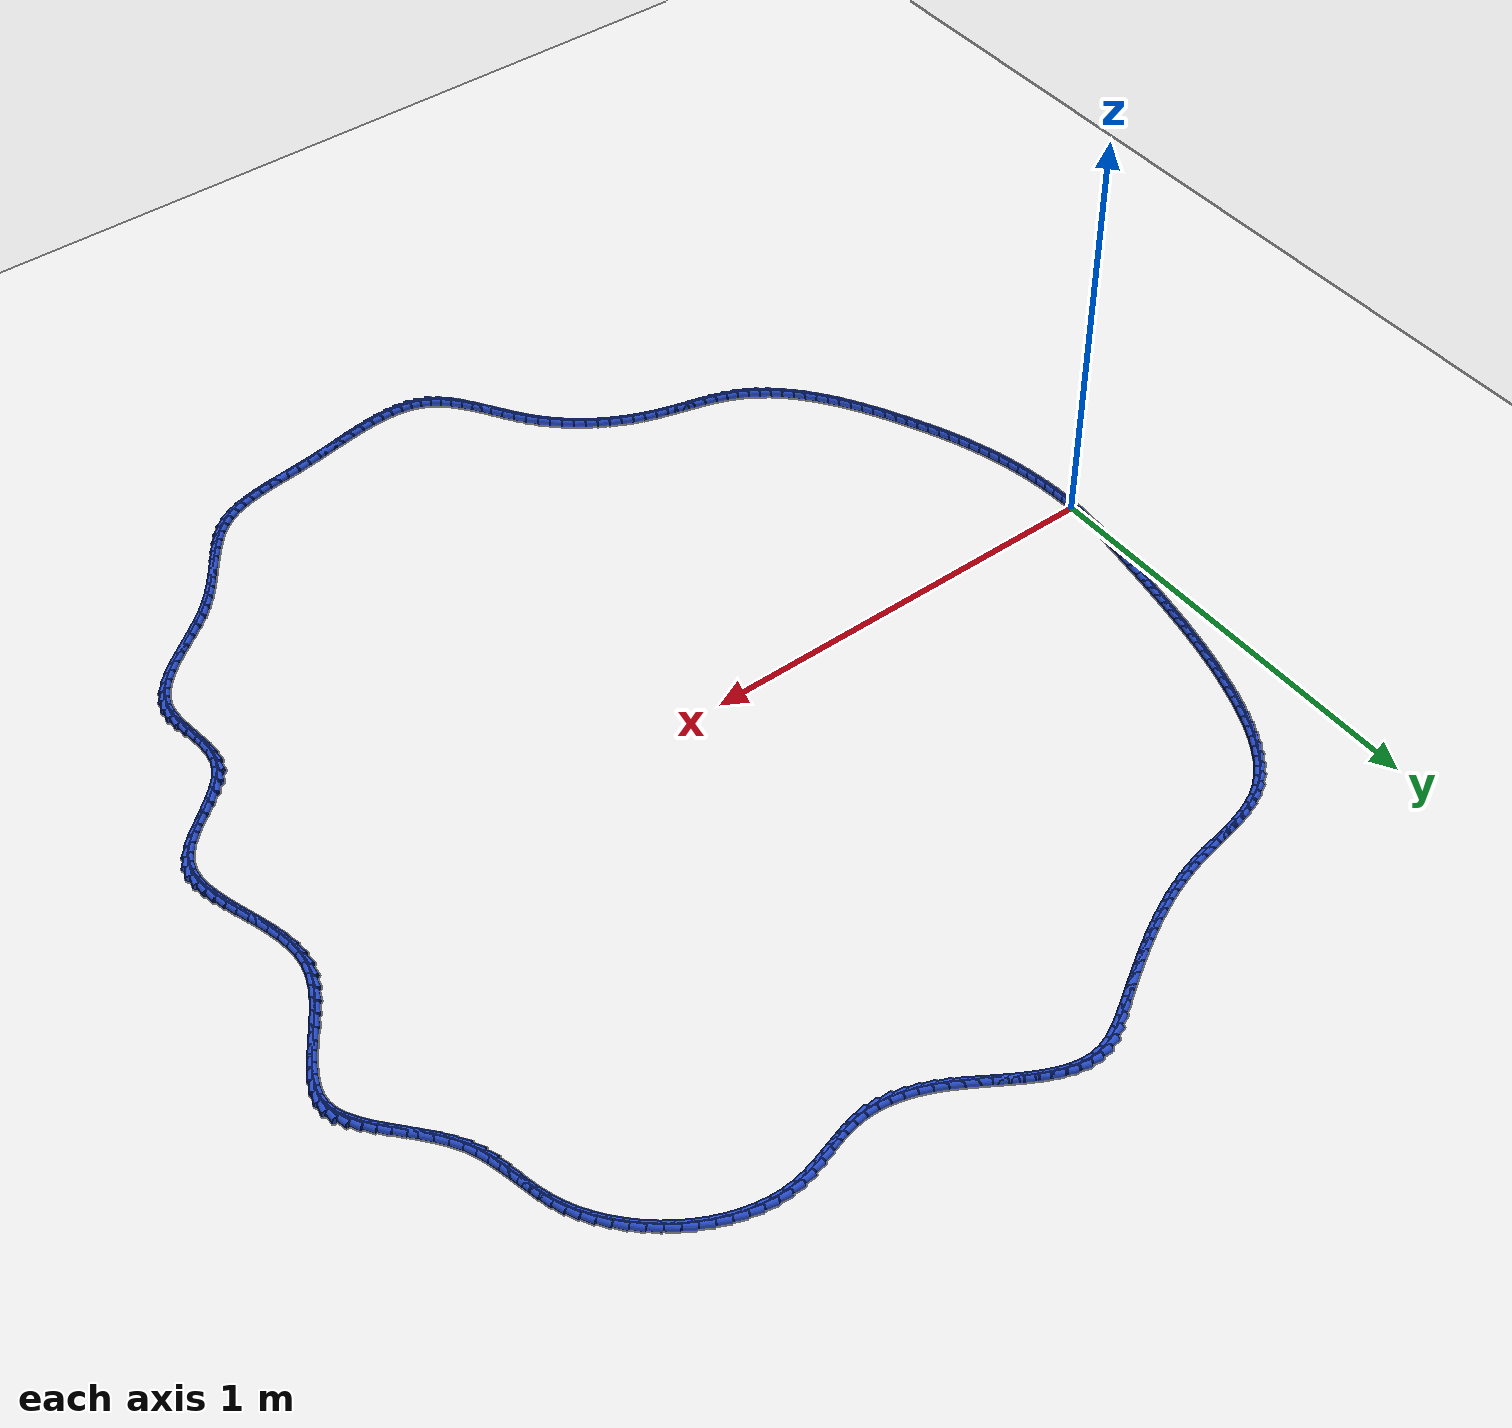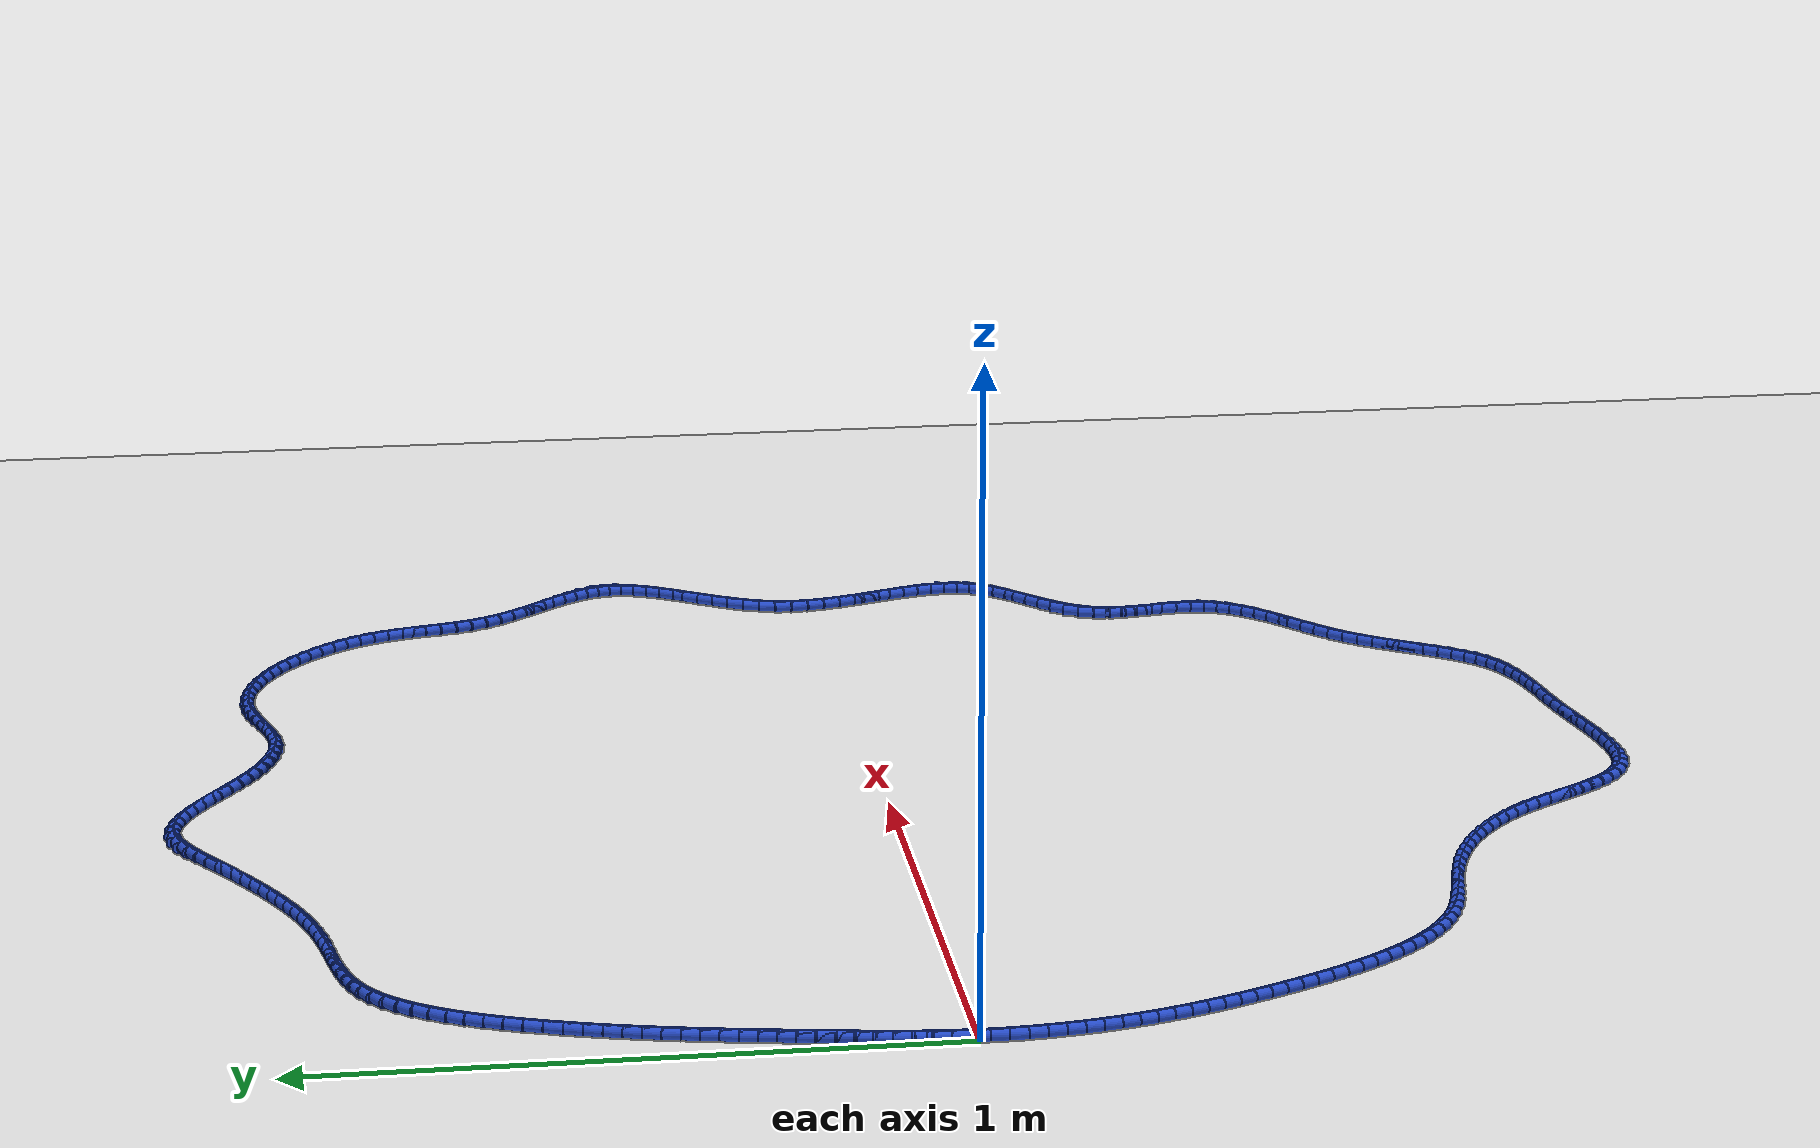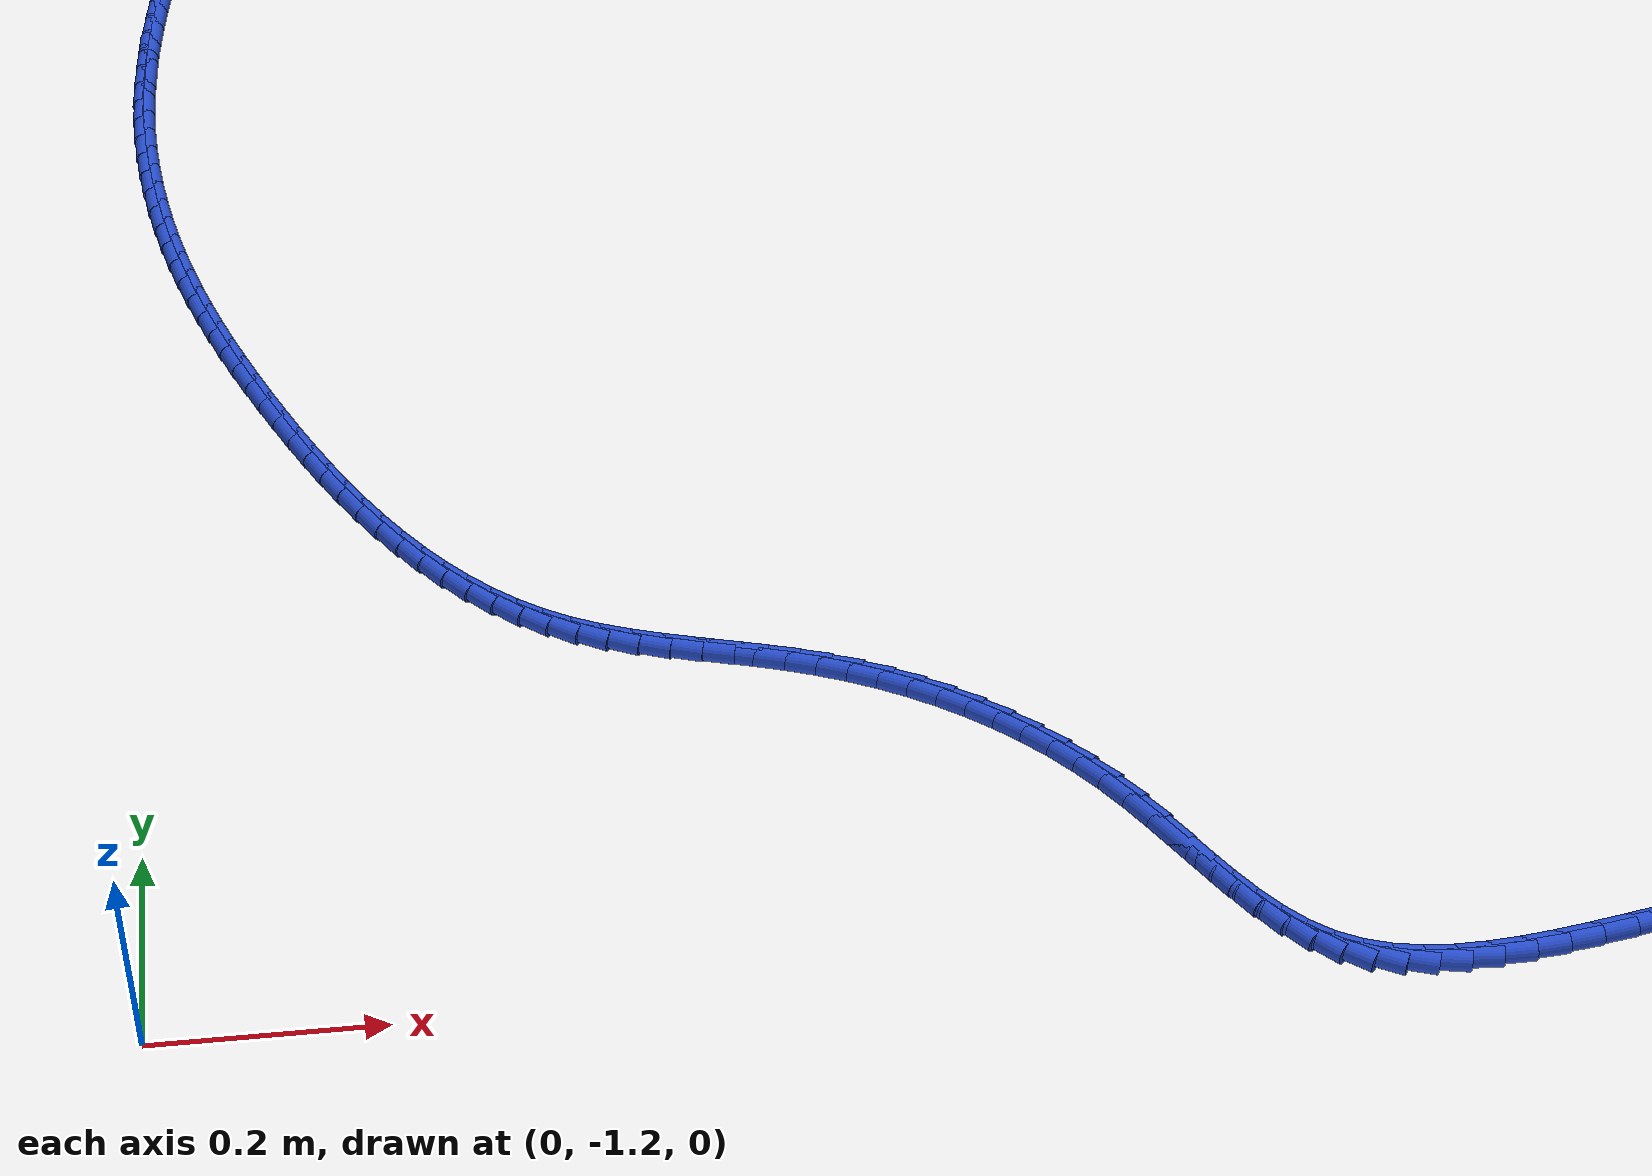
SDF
<sdf version="1.6">
 <world name="default">
  <light name="sun" type="directional">
   <pose>0 0 10 0 -0 0</pose>
   <diffuse>0.8 0.8 0.8 1</diffuse>
   <specular>0.2 0.2 0.2 1</specular>
   <attenuation>
    <range>1000</range>
    <constant>0.9</constant>
    <linear>0.01</linear>
    <quadratic>0.001</quadratic>
   </attenuation>
   <direction>-0.5 0.1 -0.9</direction>
  </light>
  <model name="ground_plane">
   <static>1</static>
   <link name="link">
    <collision name="collision">
     <geometry><plane><normal>0 0 1</normal><size>100 100</size></plane></geometry>
     <surface><friction><ode><mu>100</mu><mu2>50</mu2></ode></friction></surface>
    </collision>
    <visual name="visual">
     <cast_shadows>0</cast_shadows>
     <geometry><plane><normal>0 0 1</normal><size>100 100</size></plane></geometry>
     <material>
      <script><uri>file://media/materials/scripts/gazebo.material</uri><name>Gazebo/WhiteGlow</name></script>
     </material>
    </visual>
   </link>
  </model>
  <gravity>0 0 -9.8</gravity>
  <magnetic_field>6e-06 2.3e-05 -4.2e-05</magnetic_field>
  <atmosphere type="adiabatic"/>
  <physics name="default_physics" default="0" type="ode">
   <max_step_size>0.001</max_step_size>
   <real_time_factor>1</real_time_factor>
   <real_time_update_rate>1000</real_time_update_rate>
  </physics>
  <scene><ambient>0.4 0.4 0.4 1</ambient><background>0.7 0.7 0.7 1</background><shadows>1</shadows></scene>
  <spherical_coordinates>
   <surface_model>EARTH_WGS84</surface_model>
   <latitude_deg>0</latitude_deg>
   <longitude_deg>0</longitude_deg>
   <elevation>0</elevation>
   <heading_deg>0</heading_deg>
  </spherical_coordinates>
  <model name="line">
   <link name="link_0">
    <pose>-6.071532165918825e-18 3.469446951953614e-17 0.01 0 1.57 1.534115530524888</pose>
    <collision name="collision">
     <geometry><cylinder><radius>0.01</radius><length>0.08</length></cylinder></geometry>
    </collision>
    <visual name="visual">
     <material>
      <script><name>Gazebo/Blue</name><uri>file://media/materials/scripts/gazebo.material</uri></script>
     </material>
     <geometry><cylinder><radius>0.01</radius><length>0.08</length></cylinder></geometry>
    </visual>
   </link>
   <link name="link_1">
    <pose>0.0010214595155121423 0.027834765331651374 0.01 0 1.57 1.5033453542491406</pose>
    <collision name="collision">
     <geometry><cylinder><radius>0.01</radius><length>0.08</length></cylinder></geometry>
    </collision>
    <visual name="visual">
     <material>
      <script><name>Gazebo/Blue</name><uri>file://media/materials/scripts/gazebo.material</uri></script>
     </material>
     <geometry><cylinder><radius>0.01</radius><length>0.08</length></cylinder></geometry>
    </visual>
   </link>
   <link name="link_2">
    <pose>0.0028977489729535757 0.05560965198962347 0.01 0 1.57 1.4765638059390753</pose>
    <collision name="collision">
     <geometry><cylinder><radius>0.01</radius><length>0.08</length></cylinder></geometry>
    </collision>
    <visual name="visual">
     <material>
      <script><name>Gazebo/Blue</name><uri>file://media/materials/scripts/gazebo.material</uri></script>
     </material>
     <geometry><cylinder><radius>0.01</radius><length>0.08</length></cylinder></geometry>
    </visual>
   </link>
   <link name="link_3">
    <pose>0.00551650167215264 0.0833176744163579 0.01 0 1.57 1.4537671746762308</pose>
    <collision name="collision">
     <geometry><cylinder><radius>0.01</radius><length>0.08</length></cylinder></geometry>
    </collision>
    <visual name="visual">
     <material>
      <script><name>Gazebo/Blue</name><uri>file://media/materials/scripts/gazebo.material</uri></script>
     </material>
     <geometry><cylinder><radius>0.01</radius><length>0.08</length></cylinder></geometry>
    </visual>
   </link>
   <link name="link_4">
    <pose>0.008765350912937677 0.11095184705429631 0.01 0 1.57 1.4349370551965805</pose>
    <collision name="collision">
     <geometry><cylinder><radius>0.01</radius><length>0.08</length></cylinder></geometry>
    </collision>
    <visual name="visual">
     <material>
      <script><name>Gazebo/Blue</name><uri>file://media/materials/scripts/gazebo.material</uri></script>
     </material>
     <geometry><cylinder><radius>0.01</radius><length>0.08</length></cylinder></geometry>
    </visual>
   </link>
   <link name="link_5">
    <pose>0.012531929995137026 0.13850518434588027 0.01 0 1.57 1.4200511894583752</pose>
    <collision name="collision">
     <geometry><cylinder><radius>0.01</radius><length>0.08</length></cylinder></geometry>
    </collision>
    <visual name="visual">
     <material>
      <script><name>Gazebo/Blue</name><uri>file://media/materials/scripts/gazebo.material</uri></script>
     </material>
     <geometry><cylinder><radius>0.01</radius><length>0.08</length></cylinder></geometry>
    </visual>
   </link>
   <link name="link_6">
    <pose>0.016703872218579024 0.16597070073355139 0.01 0 1.57 1.4090923017169963</pose>
    <collision name="collision">
     <geometry><cylinder><radius>0.01</radius><length>0.08</length></cylinder></geometry>
    </collision>
    <visual name="visual">
     <material>
      <script><name>Gazebo/Blue</name><uri>file://media/materials/scripts/gazebo.material</uri></script>
     </material>
     <geometry><cylinder><radius>0.01</radius><length>0.08</length></cylinder></geometry>
    </visual>
   </link>
   <link name="link_7">
    <pose>0.02116881088309202 0.19334141065975133 0.01 0 1.57 1.4020550353025447</pose>
    <collision name="collision">
     <geometry><cylinder><radius>0.01</radius><length>0.08</length></cylinder></geometry>
    </collision>
    <visual name="visual">
     <material>
      <script><name>Gazebo/Blue</name><uri>file://media/materials/scripts/gazebo.material</uri></script>
     </material>
     <geometry><cylinder><radius>0.01</radius><length>0.08</length></cylinder></geometry>
    </visual>
   </link>
   <link name="link_8">
    <pose>0.025814379288504358 0.2206103285669217 0.01 0 1.57 1.3989224692133408</pose>
    <collision name="collision">
     <geometry><cylinder><radius>0.01</radius><length>0.08</length></cylinder></geometry>
    </collision>
    <visual name="visual">
     <material>
      <script><name>Gazebo/Blue</name><uri>file://media/materials/scripts/gazebo.material</uri></script>
     </material>
     <geometry><cylinder><radius>0.01</radius><length>0.08</length></cylinder></geometry>
    </visual>
   </link>
   <link name="link_9">
    <pose>0.0305290375935477 0.24777060784081775 0.01 0 1.57 1.3976959078714157</pose>
    <collision name="collision">
     <geometry><cylinder><radius>0.01</radius><length>0.08</length></cylinder></geometry>
    </collision>
    <visual name="visual">
     <material>
      <script><name>Gazebo/Blue</name><uri>file://media/materials/scripts/gazebo.material</uri></script>
     </material>
     <geometry><cylinder><radius>0.01</radius><length>0.08</length></cylinder></geometry>
    </visual>
   </link>
   <link name="link_10">
    <pose>0.03525954094987498 0.27482519761282703 0.01 0 1.57 1.395052872035458</pose>
    <collision name="collision">
     <geometry><cylinder><radius>0.01</radius><length>0.08</length></cylinder></geometry>
    </collision>
    <visual name="visual">
     <material>
      <script><name>Gazebo/Blue</name><uri>file://media/materials/scripts/gazebo.material</uri></script>
     </material>
     <geometry><cylinder><radius>0.01</radius><length>0.08</length></cylinder></geometry>
    </visual>
   </link>
   <link name="link_11">
    <pose>0.04004838355938719 0.30179313476624026 0.01 0 1.57 1.390678903506611</pose>
    <collision name="collision">
     <geometry><cylinder><radius>0.01</radius><length>0.08</length></cylinder></geometry>
    </collision>
    <visual name="visual">
     <material>
      <script><name>Gazebo/Blue</name><uri>file://media/materials/scripts/gazebo.material</uri></script>
     </material>
     <geometry><cylinder><radius>0.01</radius><length>0.08</length></cylinder></geometry>
    </visual>
   </link>
   <link name="link_12">
    <pose>0.04494695804197693 0.32869495145237665 0.01 0 1.57 1.3845796043517797</pose>
    <collision name="collision">
     <geometry><cylinder><radius>0.01</radius><length>0.08</length></cylinder></geometry>
    </collision>
    <visual name="visual">
     <material>
      <script><name>Gazebo/Blue</name><uri>file://media/materials/scripts/gazebo.material</uri></script>
     </material>
     <geometry><cylinder><radius>0.01</radius><length>0.08</length></cylinder></geometry>
    </visual>
   </link>
   <link name="link_13">
    <pose>0.05000665701753685 0.35555117982255613 0.01 0 1.57 1.376772325901493</pose>
    <collision name="collision">
     <geometry><cylinder><radius>0.01</radius><length>0.08</length></cylinder></geometry>
    </collision>
    <visual name="visual">
     <material>
      <script><name>Gazebo/Blue</name><uri>file://media/materials/scripts/gazebo.material</uri></script>
     </material>
     <geometry><cylinder><radius>0.01</radius><length>0.08</length></cylinder></geometry>
    </visual>
   </link>
   <link name="link_14">
    <pose>0.05527887310595958 0.38238235202809834 0.01 0 1.57 1.367286539526103</pose>
    <collision name="collision">
     <geometry><cylinder><radius>0.01</radius><length>0.08</length></cylinder></geometry>
    </collision>
    <visual name="visual">
     <material>
      <script><name>Gazebo/Blue</name><uri>file://media/materials/scripts/gazebo.material</uri></script>
     </material>
     <geometry><cylinder><radius>0.01</radius><length>0.08</length></cylinder></geometry>
    </visual>
   </link>
   <link name="link_15">
    <pose>0.06081499892713771 0.4092090002203226 0.01 0 1.57 1.356164123816054</pose>
    <collision name="collision">
     <geometry><cylinder><radius>0.01</radius><length>0.08</length></cylinder></geometry>
    </collision>
    <visual name="visual">
     <material>
      <script><name>Gazebo/Blue</name><uri>file://media/materials/scripts/gazebo.material</uri></script>
     </material>
     <geometry><cylinder><radius>0.01</radius><length>0.08</length></cylinder></geometry>
    </visual>
   </link>
   <link name="link_16">
    <pose>0.06666642710096392 0.4360516565505487 0.01 0 1.57 1.3434595279876318</pose>
    <collision name="collision">
     <geometry><cylinder><radius>0.01</radius><length>0.08</length></cylinder></geometry>
    </collision>
    <visual name="visual">
     <material>
      <script><name>Gazebo/Blue</name><uri>file://media/materials/scripts/gazebo.material</uri></script>
     </material>
     <geometry><cylinder><radius>0.01</radius><length>0.08</length></cylinder></geometry>
    </visual>
   </link>
   <link name="link_17">
    <pose>0.07288455024733081 0.4629308531700964 0.01 0 1.57 1.3292397669451796</pose>
    <collision name="collision">
     <geometry><cylinder><radius>0.01</radius><length>0.08</length></cylinder></geometry>
    </collision>
    <visual name="visual">
     <material>
      <script><name>Gazebo/Blue</name><uri>file://media/materials/scripts/gazebo.material</uri></script>
     </material>
     <geometry><cylinder><radius>0.01</radius><length>0.08</length></cylinder></geometry>
    </visual>
   </link>
   <link name="link_18">
    <pose>0.07952076098613106 0.4898671222302854 0.01 0 1.57 1.3135842027053324</pose>
    <collision name="collision">
     <geometry><cylinder><radius>0.01</radius><length>0.08</length></cylinder></geometry>
    </collision>
    <visual name="visual">
     <material>
      <script><name>Gazebo/Blue</name><uri>file://media/materials/scripts/gazebo.material</uri></script>
     </material>
     <geometry><cylinder><radius>0.01</radius><length>0.08</length></cylinder></geometry>
    </visual>
   </link>
   <link name="link_19">
    <pose>0.08662645193725724 0.5168809958824349 0.01 0 1.57 1.2965840706555858</pose>
    <collision name="collision">
     <geometry><cylinder><radius>0.01</radius><length>0.08</length></cylinder></geometry>
    </collision>
    <visual name="visual">
     <material>
      <script><name>Gazebo/Blue</name><uri>file://media/materials/scripts/gazebo.material</uri></script>
     </material>
     <geometry><cylinder><radius>0.01</radius><length>0.08</length></cylinder></geometry>
    </visual>
   </link>
   <link name="link_20">
    <pose>0.09425301572060199 0.5439930062778646 0.01 0 1.57 1.2783417178585832</pose>
    <collision name="collision">
     <geometry><cylinder><radius>0.01</radius><length>0.08</length></cylinder></geometry>
    </collision>
    <visual name="visual">
     <material>
      <script><name>Gazebo/Blue</name><uri>file://media/materials/scripts/gazebo.material</uri></script>
     </material>
     <geometry><cylinder><radius>0.01</radius><length>0.08</length></cylinder></geometry>
    </visual>
   </link>
   <link name="link_21">
    <pose>0.102451844956058 0.5712236855678947 0.01 0 1.57 1.2589695342895628</pose>
    <collision name="collision">
     <geometry><cylinder><radius>0.01</radius><length>0.08</length></cylinder></geometry>
    </collision>
    <visual name="visual">
     <material>
      <script><name>Gazebo/Blue</name><uri>file://media/materials/scripts/gazebo.material</uri></script>
     </material>
     <geometry><cylinder><radius>0.01</radius><length>0.08</length></cylinder></geometry>
    </visual>
   </link>
   <link name="link_22">
    <pose>0.1112743322635178 0.5985935659038439 0.01 0 1.57 1.2385641871770263</pose>
    <collision name="collision">
     <geometry><cylinder><radius>0.01</radius><length>0.08</length></cylinder></geometry>
    </collision>
    <visual name="visual">
     <material>
      <script><name>Gazebo/Blue</name><uri>file://media/materials/scripts/gazebo.material</uri></script>
     </material>
     <geometry><cylinder><radius>0.01</radius><length>0.08</length></cylinder></geometry>
    </visual>
   </link>
   <link name="link_23">
    <pose>0.12077209039918974 0.6261216398435565 0.01 0 1.57 1.2155396187137706</pose>
    <collision name="collision">
     <geometry><cylinder><radius>0.01</radius><length>0.08</length></cylinder></geometry>
    </collision>
    <visual name="visual">
     <material>
      <script><name>Gazebo/Blue</name><uri>file://media/materials/scripts/gazebo.material</uri></script>
     </material>
     <geometry><cylinder><radius>0.01</radius><length>0.08</length></cylinder></geometry>
    </visual>
   </link>
   <link name="link_24">
    <pose>0.13101173500701827 0.6537219724684015 0.01 0 1.57 1.1869628556771241</pose>
    <collision name="collision">
     <geometry><cylinder><radius>0.01</radius><length>0.08</length></cylinder></geometry>
    </collision>
    <visual name="visual">
     <material>
      <script><name>Gazebo/Blue</name><uri>file://media/materials/scripts/gazebo.material</uri></script>
     </material>
     <geometry><cylinder><radius>0.01</radius><length>0.08</length></cylinder></geometry>
    </visual>
   </link>
   <link name="link_25">
    <pose>0.1420842314485364 0.6811383313500713 0.01 0 1.57 1.1520744912968786</pose>
    <collision name="collision">
     <geometry><cylinder><radius>0.01</radius><length>0.08</length></cylinder></geometry>
    </collision>
    <visual name="visual">
     <material>
      <script><name>Gazebo/Blue</name><uri>file://media/materials/scripts/gazebo.material</uri></script>
     </material>
     <geometry><cylinder><radius>0.01</radius><length>0.08</length></cylinder></geometry>
    </visual>
   </link>
   <link name="link_26">
    <pose>0.15408277313884822 0.7080989014575773 0.01 0 1.57 1.1101632841195617</pose>
    <collision name="collision">
     <geometry><cylinder><radius>0.01</radius><length>0.08</length></cylinder></geometry>
    </collision>
    <visual name="visual">
     <material>
      <script><name>Gazebo/Blue</name><uri>file://media/materials/scripts/gazebo.material</uri></script>
     </material>
     <geometry><cylinder><radius>0.01</radius><length>0.08</length></cylinder></geometry>
    </visual>
   </link>
   <link name="link_27">
    <pose>0.167100553493058 0.7343318677599316 0.01 0 1.57 1.0603253264188406</pose>
    <collision name="collision">
     <geometry><cylinder><radius>0.01</radius><length>0.08</length></cylinder></geometry>
    </collision>
    <visual name="visual">
     <material>
      <script><name>Gazebo/Blue</name><uri>file://media/materials/scripts/gazebo.material</uri></script>
     </material>
     <geometry><cylinder><radius>0.01</radius><length>0.08</length></cylinder></geometry>
    </visual>
   </link>
   <link name="link_28">
    <pose>0.1812307659262695 0.7595654152261451 0.01 0 1.57 1.0014844021116316</pose>
    <collision name="collision">
     <geometry><cylinder><radius>0.01</radius><length>0.08</length></cylinder></geometry>
    </collision>
    <visual name="visual">
     <material>
      <script><name>Gazebo/Blue</name><uri>file://media/materials/scripts/gazebo.material</uri></script>
     </material>
     <geometry><cylinder><radius>0.01</radius><length>0.08</length></cylinder></geometry>
    </visual>
   </link>
   <link name="link_29">
    <pose>0.19656660385358715 0.7835277288252303 0.01 0 1.57 0.9324474969084013</pose>
    <collision name="collision">
     <geometry><cylinder><radius>0.01</radius><length>0.08</length></cylinder></geometry>
    </collision>
    <visual name="visual">
     <material>
      <script><name>Gazebo/Blue</name><uri>file://media/materials/scripts/gazebo.material</uri></script>
     </material>
     <geometry><cylinder><radius>0.01</radius><length>0.08</length></cylinder></geometry>
    </visual>
   </link>
   <link name="link_30">
    <pose>0.21320126069011486 0.805946993526198 0.01 0 1.57 0.8520262955703612</pose>
    <collision name="collision">
     <geometry><cylinder><radius>0.01</radius><length>0.08</length></cylinder></geometry>
    </collision>
    <visual name="visual">
     <material>
      <script><name>Gazebo/Blue</name><uri>file://media/materials/scripts/gazebo.material</uri></script>
     </material>
     <geometry><cylinder><radius>0.01</radius><length>0.08</length></cylinder></geometry>
    </visual>
   </link>
   <link name="link_31">
    <pose>0.23122792985095678 0.8265513942980602 0.01 0 1.57 0.7592625531002527</pose>
    <collision name="collision">
     <geometry><cylinder><radius>0.01</radius><length>0.08</length></cylinder></geometry>
    </collision>
    <visual name="visual">
     <material>
      <script><name>Gazebo/Blue</name><uri>file://media/materials/scripts/gazebo.material</uri></script>
     </material>
     <geometry><cylinder><radius>0.01</radius><length>0.08</length></cylinder></geometry>
    </visual>
   </link>
   <link name="link_32">
    <pose>0.2507398047512168 0.8450691161098283 0.01 0 1.57 0.6537845589047006</pose>
    <collision name="collision">
     <geometry><cylinder><radius>0.01</radius><length>0.08</length></cylinder></geometry>
    </collision>
    <visual name="visual">
     <material>
      <script><name>Gazebo/Blue</name><uri>file://media/materials/scripts/gazebo.material</uri></script>
     </material>
     <geometry><cylinder><radius>0.01</radius><length>0.08</length></cylinder></geometry>
    </visual>
   </link>
   <link name="link_33">
    <pose>0.2718300788059992 0.8612283439305141 0.01 0 1.57 0.5366160289273088</pose>
    <collision name="collision">
     <geometry><cylinder><radius>0.01</radius><length>0.08</length></cylinder></geometry>
    </collision>
    <visual name="visual">
     <material>
      <script><name>Gazebo/Blue</name><uri>file://media/materials/scripts/gazebo.material</uri></script>
     </material>
     <geometry><cylinder><radius>0.01</radius><length>0.08</length></cylinder></geometry>
    </visual>
   </link>
   <link name="link_34">
    <pose>0.29458775367627876 0.8747654972173478 0.01 0 1.57 0.4228962976697133</pose>
    <collision name="collision">
     <geometry><cylinder><radius>0.01</radius><length>0.08</length></cylinder></geometry>
    </collision>
    <visual name="visual">
     <material>
      <script><name>Gazebo/Blue</name><uri>file://media/materials/scripts/gazebo.material</uri></script>
     </material>
     <geometry><cylinder><radius>0.01</radius><length>0.08</length></cylinder></geometry>
    </visual>
   </link>
   <link name="link_35">
    <pose>0.3189439989150365 0.88572704859233 0.01 0 1.57 0.3311181872142504</pose>
    <collision name="collision">
     <geometry><cylinder><radius>0.01</radius><length>0.08</length></cylinder></geometry>
    </collision>
    <visual name="visual">
     <material>
      <script><name>Gazebo/Blue</name><uri>file://media/materials/scripts/gazebo.material</uri></script>
     </material>
     <geometry><cylinder><radius>0.01</radius><length>0.08</length></cylinder></geometry>
    </visual>
   </link>
   <link name="link_36">
    <pose>0.3446278696749388 0.8945565141577766 0.01 0 1.57 0.261984230877892</pose>
    <collision name="collision">
     <geometry><cylinder><radius>0.01</radius><length>0.08</length></cylinder></geometry>
    </collision>
    <visual name="visual">
     <material>
      <script><name>Gazebo/Blue</name><uri>file://media/materials/scripts/gazebo.material</uri></script>
     </material>
     <geometry><cylinder><radius>0.01</radius><length>0.08</length></cylinder></geometry>
    </visual>
   </link>
   <link name="link_37">
    <pose>0.37135520275565187 0.9017233767995259 0.01 0 1.57 0.21400467497509268</pose>
    <collision name="collision">
     <geometry><cylinder><radius>0.01</radius><length>0.08</length></cylinder></geometry>
    </collision>
    <visual name="visual">
     <material>
      <script><name>Gazebo/Blue</name><uri>file://media/materials/scripts/gazebo.material</uri></script>
     </material>
     <geometry><cylinder><radius>0.01</radius><length>0.08</length></cylinder></geometry>
    </visual>
   </link>
   <link name="link_38">
    <pose>0.3988418349568415 0.9076971194034146 0.01 0 1.57 0.18559924164322417</pose>
    <collision name="collision">
     <geometry><cylinder><radius>0.01</radius><length>0.08</length></cylinder></geometry>
    </collision>
    <visual name="visual">
     <material>
      <script><name>Gazebo/Blue</name><uri>file://media/materials/scripts/gazebo.material</uri></script>
     </material>
     <geometry><cylinder><radius>0.01</radius><length>0.08</length></cylinder></geometry>
    </visual>
   </link>
   <link name="link_39">
    <pose>0.4268036030781733 0.9129472248552806 0.01 0 1.57 0.1756303886158419</pose>
    <collision name="collision">
     <geometry><cylinder><radius>0.01</radius><length>0.08</length></cylinder></geometry>
    </collision>
    <visual name="visual">
     <material>
      <script><name>Gazebo/Blue</name><uri>file://media/materials/scripts/gazebo.material</uri></script>
     </material>
     <geometry><cylinder><radius>0.01</radius><length>0.08</length></cylinder></geometry>
    </visual>
   </link>
   <link name="link_40">
    <pose>0.45495634391931283 0.9179431760409612 0.01 0 1.57 0.1836299208196994</pose>
    <collision name="collision">
     <geometry><cylinder><radius>0.01</radius><length>0.08</length></cylinder></geometry>
    </collision>
    <visual name="visual">
     <material>
      <script><name>Gazebo/Blue</name><uri>file://media/materials/scripts/gazebo.material</uri></script>
     </material>
     <geometry><cylinder><radius>0.01</radius><length>0.08</length></cylinder></geometry>
    </visual>
   </link>
   <link name="link_41">
    <pose>0.4830158942799262 0.9231544558462943 0.01 0 1.57 0.2098558817037891</pose>
    <collision name="collision">
     <geometry><cylinder><radius>0.01</radius><length>0.08</length></cylinder></geometry>
    </collision>
    <visual name="visual">
     <material>
      <script><name>Gazebo/Blue</name><uri>file://media/materials/scripts/gazebo.material</uri></script>
     </material>
     <geometry><cylinder><radius>0.01</radius><length>0.08</length></cylinder></geometry>
    </visual>
   </link>
   <link name="link_42">
    <pose>0.5106980971659001 0.9290505376091392 0.01 0 1.57 0.2510692029521865</pose>
    <collision name="collision">
     <geometry><cylinder><radius>0.01</radius><length>0.08</length></cylinder></geometry>
    </collision>
    <visual name="visual">
     <material>
      <script><name>Gazebo/Blue</name><uri>file://media/materials/scripts/gazebo.material</uri></script>
     </material>
     <geometry><cylinder><radius>0.01</radius><length>0.08</length></cylinder></geometry>
    </visual>
   </link>
   <link name="link_43">
    <pose>0.5377856823550313 0.935997992531279 0.01 0 1.57 0.2933898754285222</pose>
    <collision name="collision">
     <geometry><cylinder><radius>0.01</radius><length>0.08</length></cylinder></geometry>
    </collision>
    <visual name="visual">
     <material>
      <script><name>Gazebo/Blue</name><uri>file://media/materials/scripts/gazebo.material</uri></script>
     </material>
     <geometry><cylinder><radius>0.01</radius><length>0.08</length></cylinder></geometry>
    </visual>
   </link>
   <link name="link_44">
    <pose>0.5642935335621662 0.9440062339589281 0.01 0 1.57 0.3333580683493871</pose>
    <collision name="collision">
     <geometry><cylinder><radius>0.01</radius><length>0.08</length></cylinder></geometry>
    </collision>
    <visual name="visual">
     <material>
      <script><name>Gazebo/Blue</name><uri>file://media/materials/scripts/gazebo.material</uri></script>
     </material>
     <geometry><cylinder><radius>0.01</radius><length>0.08</length></cylinder></geometry>
    </visual>
   </link>
   <link name="link_45">
    <pose>0.5902868686497622 0.9530072385320746 0.01 0 1.57 0.37061759378333986</pose>
    <collision name="collision">
     <geometry><cylinder><radius>0.01</radius><length>0.08</length></cylinder></geometry>
    </collision>
    <visual name="visual">
     <material>
      <script><name>Gazebo/Blue</name><uri>file://media/materials/scripts/gazebo.material</uri></script>
     </material>
     <geometry><cylinder><radius>0.01</radius><length>0.08</length></cylinder></geometry>
    </visual>
   </link>
   <link name="link_46">
    <pose>0.6158309054802777 0.9629329828907063 0.01 0 1.57 0.4048791040957788</pose>
    <collision name="collision">
     <geometry><cylinder><radius>0.01</radius><length>0.08</length></cylinder></geometry>
    </collision>
    <visual name="visual">
     <material>
      <script><name>Gazebo/Blue</name><uri>file://media/materials/scripts/gazebo.material</uri></script>
     </material>
     <geometry><cylinder><radius>0.01</radius><length>0.08</length></cylinder></geometry>
    </visual>
   </link>
   <link name="link_47">
    <pose>0.6409908619161702 0.9737154436748117 0.01 0 1.57 0.4359209444267615</pose>
    <collision name="collision">
     <geometry><cylinder><radius>0.01</radius><length>0.08</length></cylinder></geometry>
    </collision>
    <visual name="visual">
     <material>
      <script><name>Gazebo/Blue</name><uri>file://media/materials/scripts/gazebo.material</uri></script>
     </material>
     <geometry><cylinder><radius>0.01</radius><length>0.08</length></cylinder></geometry>
    </visual>
   </link>
   <link name="link_48">
    <pose>0.6658319558198971 0.9852865975243785 0.01 0 1.57 0.46358575237568</pose>
    <collision name="collision">
     <geometry><cylinder><radius>0.01</radius><length>0.08</length></cylinder></geometry>
    </collision>
    <visual name="visual">
     <material>
      <script><name>Gazebo/Blue</name><uri>file://media/materials/scripts/gazebo.material</uri></script>
     </material>
     <geometry><cylinder><radius>0.01</radius><length>0.08</length></cylinder></geometry>
    </visual>
   </link>
   <link name="link_49">
    <pose>0.6904194050539163 0.9975784210793948 0.01 0 1.57 0.4877740684129644</pose>
    <collision name="collision">
     <geometry><cylinder><radius>0.01</radius><length>0.08</length></cylinder></geometry>
    </collision>
    <visual name="visual">
     <material>
      <script><name>Gazebo/Blue</name><uri>file://media/materials/scripts/gazebo.material</uri></script>
     </material>
     <geometry><cylinder><radius>0.01</radius><length>0.08</length></cylinder></geometry>
    </visual>
   </link>
   <link name="link_50">
    <pose>0.7148184274806861 1.0105228909798492 0.01 0 1.57 0.508436257500345</pose>
    <collision name="collision">
     <geometry><cylinder><radius>0.01</radius><length>0.08</length></cylinder></geometry>
    </collision>
    <visual name="visual">
     <material>
      <script><name>Gazebo/Blue</name><uri>file://media/materials/scripts/gazebo.material</uri></script>
     </material>
     <geometry><cylinder><radius>0.01</radius><length>0.08</length></cylinder></geometry>
    </visual>
   </link>
   <link name="link_51">
    <pose>0.7390942409626634 1.0240519838657287 0.01 0 1.57 0.5255638802514572</pose>
    <collision name="collision">
     <geometry><cylinder><radius>0.01</radius><length>0.08</length></cylinder></geometry>
    </collision>
    <visual name="visual">
     <material>
      <script><name>Gazebo/Blue</name><uri>file://media/materials/scripts/gazebo.material</uri></script>
     </material>
     <geometry><cylinder><radius>0.01</radius><length>0.08</length></cylinder></geometry>
    </visual>
   </link>
   <link name="link_52">
    <pose>0.7633120633623065 1.0380976763770224 0.01 0 1.57 0.5391813861630207</pose>
    <collision name="collision">
     <geometry><cylinder><radius>0.01</radius><length>0.08</length></cylinder></geometry>
    </collision>
    <visual name="visual">
     <material>
      <script><name>Gazebo/Blue</name><uri>file://media/materials/scripts/gazebo.material</uri></script>
     </material>
     <geometry><cylinder><radius>0.01</radius><length>0.08</length></cylinder></geometry>
    </visual>
   </link>
   <link name="link_53">
    <pose>0.7875371125420727 1.0525919451537178 0.01 0 1.57 0.549338712858866</pose>
    <collision name="collision">
     <geometry><cylinder><radius>0.01</radius><length>0.08</length></cylinder></geometry>
    </collision>
    <visual name="visual">
     <material>
      <script><name>Gazebo/Blue</name><uri>file://media/materials/scripts/gazebo.material</uri></script>
     </material>
     <geometry><cylinder><radius>0.01</radius><length>0.08</length></cylinder></geometry>
    </visual>
   </link>
   <link name="link_54">
    <pose>0.8118346063644202 1.067466766835803 0.01 0 1.57 0.5561051167401195</pose>
    <collision name="collision">
     <geometry><cylinder><radius>0.01</radius><length>0.08</length></cylinder></geometry>
    </collision>
    <visual name="visual">
     <material>
      <script><name>Gazebo/Blue</name><uri>file://media/materials/scripts/gazebo.material</uri></script>
     </material>
     <geometry><cylinder><radius>0.01</radius><length>0.08</length></cylinder></geometry>
    </visual>
   </link>
   <link name="link_55">
    <pose>0.8362697626918066 1.082654118063267 0.01 0 1.57 0.5594019995564627</pose>
    <collision name="collision">
     <geometry><cylinder><radius>0.01</radius><length>0.08</length></cylinder></geometry>
    </collision>
    <visual name="visual">
     <material>
      <script><name>Gazebo/Blue</name><uri>file://media/materials/scripts/gazebo.material</uri></script>
     </material>
     <geometry><cylinder><radius>0.01</radius><length>0.08</length></cylinder></geometry>
    </visual>
   </link>
   <link name="link_56">
    <pose>0.8609070505375509 1.098079937723464 0.01 0 1.57 0.548538417822134</pose>
    <collision name="collision">
     <geometry><cylinder><radius>0.01</radius><length>0.08</length></cylinder></geometry>
    </collision>
    <visual name="visual">
     <material>
      <script><name>Gazebo/Blue</name><uri>file://media/materials/scripts/gazebo.material</uri></script>
     </material>
     <geometry><cylinder><radius>0.01</radius><length>0.08</length></cylinder></geometry>
    </visual>
   </link>
   <link name="link_57">
    <pose>0.8857610759110623 1.1132681338170665 0.01 0 1.57 0.5051282833225889</pose>
    <collision name="collision">
     <geometry><cylinder><radius>0.01</radius><length>0.08</length></cylinder></geometry>
    </collision>
    <visual name="visual">
     <material>
      <script><name>Gazebo/Blue</name><uri>file://media/materials/scripts/gazebo.material</uri></script>
     </material>
     <geometry><cylinder><radius>0.01</radius><length>0.08</length></cylinder></geometry>
    </visual>
   </link>
   <link name="link_58">
    <pose>0.9107661793686341 1.1270954573594927 0.01 0 1.57 0.4227598619854854</pose>
    <collision name="collision">
     <geometry><cylinder><radius>0.01</radius><length>0.08</length></cylinder></geometry>
    </collision>
    <visual name="visual">
     <material>
      <script><name>Gazebo/Blue</name><uri>file://media/materials/scripts/gazebo.material</uri></script>
     </material>
     <geometry><cylinder><radius>0.01</radius><length>0.08</length></cylinder></geometry>
    </visual>
   </link>
   <link name="link_59">
    <pose>0.9358494367512108 1.1383800860808817 0.01 0 1.57 0.2926837585913416</pose>
    <collision name="collision">
     <geometry><cylinder><radius>0.01</radius><length>0.08</length></cylinder></geometry>
    </collision>
    <visual name="visual">
     <material>
      <script><name>Gazebo/Blue</name><uri>file://media/materials/scripts/gazebo.material</uri></script>
     </material>
     <geometry><cylinder><radius>0.01</radius><length>0.08</length></cylinder></geometry>
    </visual>
   </link>
   <link name="link_60">
    <pose>0.9609379238997373 1.1459401977113752 0.01 0 1.57 0.11414078489687311</pose>
    <collision name="collision">
     <geometry><cylinder><radius>0.01</radius><length>0.08</length></cylinder></geometry>
    </collision>
    <visual name="visual">
     <material>
      <script><name>Gazebo/Blue</name><uri>file://media/materials/scripts/gazebo.material</uri></script>
     </material>
     <geometry><cylinder><radius>0.01</radius><length>0.08</length></cylinder></geometry>
    </visual>
   </link>
   <link name="link_61">
    <pose>0.9859719474398841 1.1488100746781469 0.01 0 1.57 -0.06456572657748733</pose>
    <collision name="collision">
     <geometry><cylinder><radius>0.01</radius><length>0.08</length></cylinder></geometry>
    </collision>
    <visual name="visual">
     <material>
      <script><name>Gazebo/Blue</name><uri>file://media/materials/scripts/gazebo.material</uri></script>
     </material>
     <geometry><cylinder><radius>0.01</radius><length>0.08</length></cylinder></geometry>
    </visual>
   </link>
   <link name="link_62">
    <pose>1.0109634603609354 1.1471942335270642 0.01 0 1.57 -0.2167809324883633</pose>
    <collision name="collision">
     <geometry><cylinder><radius>0.01</radius><length>0.08</length></cylinder></geometry>
    </collision>
    <visual name="visual">
     <material>
      <script><name>Gazebo/Blue</name><uri>file://media/materials/scripts/gazebo.material</uri></script>
     </material>
     <geometry><cylinder><radius>0.01</radius><length>0.08</length></cylinder></geometry>
    </visual>
   </link>
   <link name="link_63">
    <pose>1.0359485550609202 1.141691471243283 0.01 0 1.57 -0.3379353653395556</pose>
    <collision name="collision">
     <geometry><cylinder><radius>0.01</radius><length>0.08</length></cylinder></geometry>
    </collision>
    <visual name="visual">
     <material>
      <script><name>Gazebo/Blue</name><uri>file://media/materials/scripts/gazebo.material</uri></script>
     </material>
     <geometry><cylinder><radius>0.01</radius><length>0.08</length></cylinder></geometry>
    </visual>
   </link>
   <link name="link_64">
    <pose>1.060963342320641 1.1329008850665443 0.01 0 1.57 -0.42923634505481106</pose>
    <collision name="collision">
     <geometry><cylinder><radius>0.01</radius><length>0.08</length></cylinder></geometry>
    </collision>
    <visual name="visual">
     <material>
      <script><name>Gazebo/Blue</name><uri>file://media/materials/scripts/gazebo.material</uri></script>
     </material>
     <geometry><cylinder><radius>0.01</radius><length>0.08</length></cylinder></geometry>
    </visual>
   </link>
   <link name="link_65">
    <pose>1.086043932920902 1.121421572236589 0.01 0 1.57 -0.4942224501571923</pose>
    <collision name="collision">
     <geometry><cylinder><radius>0.01</radius><length>0.08</length></cylinder></geometry>
    </collision>
    <visual name="visual">
     <material>
      <script><name>Gazebo/Blue</name><uri>file://media/materials/scripts/gazebo.material</uri></script>
     </material>
     <geometry><cylinder><radius>0.01</radius><length>0.08</length></cylinder></geometry>
    </visual>
   </link>
   <link name="link_66">
    <pose>1.1112264376425058 1.1078526299931568 0.01 0 1.57 -0.5365528724173769</pose>
    <collision name="collision">
     <geometry><cylinder><radius>0.01</radius><length>0.08</length></cylinder></geometry>
    </collision>
    <visual name="visual">
     <material>
      <script><name>Gazebo/Blue</name><uri>file://media/materials/scripts/gazebo.material</uri></script>
     </material>
     <geometry><cylinder><radius>0.01</radius><length>0.08</length></cylinder></geometry>
    </visual>
   </link>
   <link name="link_67">
    <pose>1.1365469672662563 1.0927931555759887 0.01 0 1.57 -0.5590714431619331</pose>
    <collision name="collision">
     <geometry><cylinder><radius>0.01</radius><length>0.08</length></cylinder></geometry>
    </collision>
    <visual name="visual">
     <material>
      <script><name>Gazebo/Blue</name><uri>file://media/materials/scripts/gazebo.material</uri></script>
     </material>
     <geometry><cylinder><radius>0.01</radius><length>0.08</length></cylinder></geometry>
    </visual>
   </link>
   <link name="link_68">
    <pose>1.1620416325729557 1.0768422462248255 0.01 0 1.57 -0.5635544433851493</pose>
    <collision name="collision">
     <geometry><cylinder><radius>0.01</radius><length>0.08</length></cylinder></geometry>
    </collision>
    <visual name="visual">
     <material>
      <script><name>Gazebo/Blue</name><uri>file://media/materials/scripts/gazebo.material</uri></script>
     </material>
     <geometry><cylinder><radius>0.01</radius><length>0.08</length></cylinder></geometry>
    </visual>
   </link>
   <link name="link_69">
    <pose>1.187746544343408 1.0605989991794076 0.01 0 1.57 -0.5507174615632591</pose>
    <collision name="collision">
     <geometry><cylinder><radius>0.01</radius><length>0.08</length></cylinder></geometry>
    </collision>
    <visual name="visual">
     <material>
      <script><name>Gazebo/Blue</name><uri>file://media/materials/scripts/gazebo.material</uri></script>
     </material>
     <geometry><cylinder><radius>0.01</radius><length>0.08</length></cylinder></geometry>
    </visual>
   </link>
   <link name="link_70">
    <pose>1.2136978133584164 1.0446625116794752 0.01 0 1.57 -0.5202926035390121</pose>
    <collision name="collision">
     <geometry><cylinder><radius>0.01</radius><length>0.08</length></cylinder></geometry>
    </collision>
    <visual name="visual">
     <material>
      <script><name>Gazebo/Blue</name><uri>file://media/materials/scripts/gazebo.material</uri></script>
     </material>
     <geometry><cylinder><radius>0.01</radius><length>0.08</length></cylinder></geometry>
    </visual>
   </link>
   <link name="link_71">
    <pose>1.2399315503987833 1.0296318809647693 0.01 0 1.57 -0.47113711661729996</pose>
    <collision name="collision">
     <geometry><cylinder><radius>0.01</radius><length>0.08</length></cylinder></geometry>
    </collision>
    <visual name="visual">
     <material>
      <script><name>Gazebo/Blue</name><uri>file://media/materials/scripts/gazebo.material</uri></script>
     </material>
     <geometry><cylinder><radius>0.01</radius><length>0.08</length></cylinder></geometry>
    </visual>
   </link>
   <link name="link_72">
    <pose>1.2664838662453124 1.0161062042750304 0.01 0 1.57 -0.4027305709951662</pose>
    <collision name="collision">
     <geometry><cylinder><radius>0.01</radius><length>0.08</length></cylinder></geometry>
    </collision>
    <visual name="visual">
     <material>
      <script><name>Gazebo/Blue</name><uri>file://media/materials/scripts/gazebo.material</uri></script>
     </material>
     <geometry><cylinder><radius>0.01</radius><length>0.08</length></cylinder></geometry>
    </visual>
   </link>
   <link name="link_73">
    <pose>1.2933767721583673 1.0046494063245723 0.01 0 1.57 -0.32218533567373275</pose>
    <collision name="collision">
     <geometry><cylinder><radius>0.01</radius><length>0.08</length></cylinder></geometry>
    </collision>
    <visual name="visual">
     <material>
      <script><name>Gazebo/Blue</name><uri>file://media/materials/scripts/gazebo.material</uri></script>
     </material>
     <geometry><cylinder><radius>0.01</radius><length>0.08</length></cylinder></geometry>
    </visual>
   </link>
   <link name="link_74">
    <pose>1.3205352836709827 0.9955834472374644 0.01 0 1.57 -0.23211272492293178</pose>
    <collision name="collision">
     <geometry><cylinder><radius>0.01</radius><length>0.08</length></cylinder></geometry>
    </collision>
    <visual name="visual">
     <material>
      <script><name>Gazebo/Blue</name><uri>file://media/materials/scripts/gazebo.material</uri></script>
     </material>
     <geometry><cylinder><radius>0.01</radius><length>0.08</length></cylinder></geometry>
    </visual>
   </link>
   <link name="link_75">
    <pose>1.347843611310174 0.9891284953698999 0.01 0 1.57 -0.13177891272450698</pose>
    <collision name="collision">
     <geometry><cylinder><radius>0.01</radius><length>0.08</length></cylinder></geometry>
    </collision>
    <visual name="visual">
     <material>
      <script><name>Gazebo/Blue</name><uri>file://media/materials/scripts/gazebo.material</uri></script>
     </material>
     <geometry><cylinder><radius>0.01</radius><length>0.08</length></cylinder></geometry>
    </visual>
   </link>
   <link name="link_76">
    <pose>1.3751858238670163 0.9855043655049885 0.01 0 1.57 -0.021034666077424772</pose>
    <collision name="collision">
     <geometry><cylinder><radius>0.01</radius><length>0.08</length></cylinder></geometry>
    </collision>
    <visual name="visual">
     <material>
      <script><name>Gazebo/Blue</name><uri>file://media/materials/scripts/gazebo.material</uri></script>
     </material>
     <geometry><cylinder><radius>0.01</radius><length>0.08</length></cylinder></geometry>
    </visual>
   </link>
   <link name="link_77">
    <pose>1.402445990132587 0.9849308724258392 0.01 0 1.57 0.09747089174126566</pose>
    <collision name="collision">
     <geometry><cylinder><radius>0.01</radius><length>0.08</length></cylinder></geometry>
    </collision>
    <visual name="visual">
     <material>
      <script><name>Gazebo/Blue</name><uri>file://media/materials/scripts/gazebo.material</uri></script>
     </material>
     <geometry><cylinder><radius>0.01</radius><length>0.08</length></cylinder></geometry>
    </visual>
   </link>
   <link name="link_78">
    <pose>1.42951725263551 0.9875779206633518 0.01 0 1.57 0.1971548235660818</pose>
    <collision name="collision">
     <geometry><cylinder><radius>0.01</radius><length>0.08</length></cylinder></geometry>
    </collision>
    <visual name="visual">
     <material>
      <script><name>Gazebo/Blue</name><uri>file://media/materials/scripts/gazebo.material</uri></script>
     </material>
     <geometry><cylinder><radius>0.01</radius><length>0.08</length></cylinder></geometry>
    </visual>
   </link>
   <link name="link_79">
    <pose>1.4564136424800946 0.9929504650219272 0.01 0 1.57 0.25982197745513524</pose>
    <collision name="collision">
     <geometry><cylinder><radius>0.01</radius><length>0.08</length></cylinder></geometry>
    </collision>
    <visual name="visual">
     <material>
      <script><name>Gazebo/Blue</name><uri>file://media/materials/scripts/gazebo.material</uri></script>
     </material>
     <geometry><cylinder><radius>0.01</radius><length>0.08</length></cylinder></geometry>
    </visual>
   </link>
   <link name="link_80">
    <pose>1.4832351827330772 1.0000804600114879 0.01 0 1.57 0.2864849702965535</pose>
    <collision name="collision">
     <geometry><cylinder><radius>0.01</radius><length>0.08</length></cylinder></geometry>
    </collision>
    <visual name="visual">
     <material>
      <script><name>Gazebo/Blue</name><uri>file://media/materials/scripts/gazebo.material</uri></script>
     </material>
     <geometry><cylinder><radius>0.01</radius><length>0.08</length></cylinder></geometry>
    </visual>
   </link>
   <link name="link_81">
    <pose>1.5100837360492592 1.0079897414556096 0.01 0 1.57 0.27838762405035156</pose>
    <collision name="collision">
     <geometry><cylinder><radius>0.01</radius><length>0.08</length></cylinder></geometry>
    </collision>
    <visual name="visual">
     <material>
      <script><name>Gazebo/Blue</name><uri>file://media/materials/scripts/gazebo.material</uri></script>
     </material>
     <geometry><cylinder><radius>0.01</radius><length>0.08</length></cylinder></geometry>
    </visual>
   </link>
   <link name="link_82">
    <pose>1.537061165083442 1.015700145177866 0.01 0 1.57 0.23566319123228607</pose>
    <collision name="collision">
     <geometry><cylinder><radius>0.01</radius><length>0.08</length></cylinder></geometry>
    </collision>
    <visual name="visual">
     <material>
      <script><name>Gazebo/Blue</name><uri>file://media/materials/scripts/gazebo.material</uri></script>
     </material>
     <geometry><cylinder><radius>0.01</radius><length>0.08</length></cylinder></geometry>
    </visual>
   </link>
   <link name="link_83">
    <pose>1.5642693324904269 1.0222335070018325 0.01 0 1.57 0.15765080355639802</pose>
    <collision name="collision">
     <geometry><cylinder><radius>0.01</radius><length>0.08</length></cylinder></geometry>
    </collision>
    <visual name="visual">
     <material>
      <script><name>Gazebo/Blue</name><uri>file://media/materials/scripts/gazebo.material</uri></script>
     </material>
     <geometry><cylinder><radius>0.01</radius><length>0.08</length></cylinder></geometry>
    </visual>
   </link>
   <link name="link_84">
    <pose>1.5918101009250145 1.026611662751083 0.01 0 1.57 0.050052059470819775</pose>
    <collision name="collision">
     <geometry><cylinder><radius>0.01</radius><length>0.08</length></cylinder></geometry>
    </collision>
    <visual name="visual">
     <material>
      <script><name>Gazebo/Blue</name><uri>file://media/materials/scripts/gazebo.material</uri></script>
     </material>
     <geometry><cylinder><radius>0.01</radius><length>0.08</length></cylinder></geometry>
    </visual>
   </link>
   <link name="link_85">
    <pose>1.6197450706678078 1.0280110342857405 0.01 0 1.57 -0.05814804762128849</pose>
    <collision name="collision">
     <geometry><cylinder><radius>0.01</radius><length>0.08</length></cylinder></geometry>
    </collision>
    <visual name="visual">
     <material>
      <script><name>Gazebo/Blue</name><uri>file://media/materials/scripts/gazebo.material</uri></script>
     </material>
     <geometry><cylinder><radius>0.01</radius><length>0.08</length></cylinder></geometry>
    </visual>
   </link>
   <link name="link_86">
    <pose>1.6479374263480122 1.02636985371058 0.01 0 1.57 -0.15827299407377377</pose>
    <collision name="collision">
     <geometry><cylinder><radius>0.01</radius><length>0.08</length></cylinder></geometry>
    </collision>
    <visual name="visual">
     <material>
      <script><name>Gazebo/Blue</name><uri>file://media/materials/scripts/gazebo.material</uri></script>
     </material>
     <geometry><cylinder><radius>0.01</radius><length>0.08</length></cylinder></geometry>
    </visual>
   </link>
   <link name="link_87">
    <pose>1.6761893361448488 1.0218606237454344 0.01 0 1.57 -0.2508722938636762</pose>
    <collision name="collision">
     <geometry><cylinder><radius>0.01</radius><length>0.08</length></cylinder></geometry>
    </collision>
    <visual name="visual">
     <material>
      <script><name>Gazebo/Blue</name><uri>file://media/materials/scripts/gazebo.material</uri></script>
     </material>
     <geometry><cylinder><radius>0.01</radius><length>0.08</length></cylinder></geometry>
    </visual>
   </link>
   <link name="link_88">
    <pose>1.704302951571053 1.0146559111005513 0.01 0 1.57 -0.33685162620471876</pose>
    <collision name="collision">
     <geometry><cylinder><radius>0.01</radius><length>0.08</length></cylinder></geometry>
    </collision>
    <visual name="visual">
     <material>
      <script><name>Gazebo/Blue</name><uri>file://media/materials/scripts/gazebo.material</uri></script>
     </material>
     <geometry><cylinder><radius>0.01</radius><length>0.08</length></cylinder></geometry>
    </visual>
   </link>
   <link name="link_89">
    <pose>1.7320804241393608 1.0049282824861778 0.01 0 1.57 -0.41729717133138317</pose>
    <collision name="collision">
     <geometry><cylinder><radius>0.01</radius><length>0.08</length></cylinder></geometry>
    </collision>
    <visual name="visual">
     <material>
      <script><name>Gazebo/Blue</name><uri>file://media/materials/scripts/gazebo.material</uri></script>
     </material>
     <geometry><cylinder><radius>0.01</radius><length>0.08</length></cylinder></geometry>
    </visual>
   </link>
   <link name="link_90">
    <pose>1.7593239053625072 0.9928503046125606 0.01 0 1.57 -0.4933640058254891</pose>
    <collision name="collision">
     <geometry><cylinder><radius>0.01</radius><length>0.08</length></cylinder></geometry>
    </collision>
    <visual name="visual">
     <material>
      <script><name>Gazebo/Blue</name><uri>file://media/materials/scripts/gazebo.material</uri></script>
     </material>
     <geometry><cylinder><radius>0.01</radius><length>0.08</length></cylinder></geometry>
    </visual>
   </link>
   <link name="link_91">
    <pose>1.7858355467532279 0.9785945441899474 0.01 0 1.57 -0.5662157608824502</pose>
    <collision name="collision">
     <geometry><cylinder><radius>0.01</radius><length>0.08</length></cylinder></geometry>
    </collision>
    <visual name="visual">
     <material>
      <script><name>Gazebo/Blue</name><uri>file://media/materials/scripts/gazebo.material</uri></script>
     </material>
     <geometry><cylinder><radius>0.01</radius><length>0.08</length></cylinder></geometry>
    </visual>
   </link>
   <link name="link_92">
    <pose>1.8114174998242594 0.9623335679285859 0.01 0 1.57 -0.6370004987460441</pose>
    <collision name="collision">
     <geometry><cylinder><radius>0.01</radius><length>0.08</length></cylinder></geometry>
    </collision>
    <visual name="visual">
     <material>
      <script><name>Gazebo/Blue</name><uri>file://media/materials/scripts/gazebo.material</uri></script>
     </material>
     <geometry><cylinder><radius>0.01</radius><length>0.08</length></cylinder></geometry>
    </visual>
   </link>
   <link name="link_93">
    <pose>1.8358719160883352 0.9442399425387225 0.01 0 1.57 -0.7068495767034636</pose>
    <collision name="collision">
     <geometry><cylinder><radius>0.01</radius><length>0.08</length></cylinder></geometry>
    </collision>
    <visual name="visual">
     <material>
      <script><name>Gazebo/Blue</name><uri>file://media/materials/scripts/gazebo.material</uri></script>
     </material>
     <geometry><cylinder><radius>0.01</radius><length>0.08</length></cylinder></geometry>
    </visual>
   </link>
   <link name="link_94">
    <pose>1.8590009470581927 0.924486234730605 0.01 0 1.57 -0.7768896400871864</pose>
    <collision name="collision">
     <geometry><cylinder><radius>0.01</radius><length>0.08</length></cylinder></geometry>
    </collision>
    <visual name="visual">
     <material>
      <script><name>Gazebo/Blue</name><uri>file://media/materials/scripts/gazebo.material</uri></script>
     </material>
     <geometry><cylinder><radius>0.01</radius><length>0.08</length></cylinder></geometry>
    </visual>
   </link>
   <link name="link_95">
    <pose>1.880606744246566 0.9032450112144803 0.01 0 1.57 -0.8482606035426986</pose>
    <collision name="collision">
     <geometry><cylinder><radius>0.01</radius><length>0.08</length></cylinder></geometry>
    </collision>
    <visual name="visual">
     <material>
      <script><name>Gazebo/Blue</name><uri>file://media/materials/scripts/gazebo.material</uri></script>
     </material>
     <geometry><cylinder><radius>0.01</radius><length>0.08</length></cylinder></geometry>
    </visual>
   </link>
   <link name="link_96">
    <pose>1.9004914591661917 0.8806888387005962 0.01 0 1.57 -0.9221337591094008</pose>
    <collision name="collision">
     <geometry><cylinder><radius>0.01</radius><length>0.08</length></cylinder></geometry>
    </collision>
    <visual name="visual">
     <material>
      <script><name>Gazebo/Blue</name><uri>file://media/materials/scripts/gazebo.material</uri></script>
     </material>
     <geometry><cylinder><radius>0.01</radius><length>0.08</length></cylinder></geometry>
    </visual>
   </link>
   <link name="link_97">
    <pose>1.918457243329805 0.8569902838991995 0.01 0 1.57 -0.9997237342342028</pose>
    <collision name="collision">
     <geometry><cylinder><radius>0.01</radius><length>0.08</length></cylinder></geometry>
    </collision>
    <visual name="visual">
     <material>
      <script><name>Gazebo/Blue</name><uri>file://media/materials/scripts/gazebo.material</uri></script>
     </material>
     <geometry><cylinder><radius>0.01</radius><length>0.08</length></cylinder></geometry>
    </visual>
   </link>
   <link name="link_98">
    <pose>1.934306248250141 0.8323219135205376 0.01 0 1.57 -1.0822857770014065</pose>
    <collision name="collision">
     <geometry><cylinder><radius>0.01</radius><length>0.08</length></cylinder></geometry>
    </collision>
    <visual name="visual">
     <material>
      <script><name>Gazebo/Blue</name><uri>file://media/materials/scripts/gazebo.material</uri></script>
     </material>
     <geometry><cylinder><radius>0.01</radius><length>0.08</length></cylinder></geometry>
    </visual>
   </link>
   <link name="link_99">
    <pose>1.9478406254399359 0.8068562942748574 0.01 0 1.57 -1.170811215280692</pose>
    <collision name="collision">
     <geometry><cylinder><radius>0.01</radius><length>0.08</length></cylinder></geometry>
    </collision>
    <visual name="visual">
     <material>
      <script><name>Gazebo/Blue</name><uri>file://media/materials/scripts/gazebo.material</uri></script>
     </material>
     <geometry><cylinder><radius>0.01</radius><length>0.08</length></cylinder></geometry>
    </visual>
   </link>
   <link name="link_100">
    <pose>1.9588709462325842 0.7807660492540565 0.01 0 1.57 -1.2527446344039386</pose>
    <collision name="collision">
     <geometry><cylinder><radius>0.01</radius><length>0.08</length></cylinder></geometry>
    </collision>
    <visual name="visual">
     <material>
      <script><name>Gazebo/Blue</name><uri>file://media/materials/scripts/gazebo.material</uri></script>
     </material>
     <geometry><cylinder><radius>0.01</radius><length>0.08</length></cylinder></geometry>
    </visual>
   </link>
   <link name="link_101">
    <pose>1.967608527910078 0.7542264850653428 0.01 0 1.57 -1.3076033278958545</pose>
    <collision name="collision">
     <geometry><cylinder><radius>0.01</radius><length>0.08</length></cylinder></geometry>
    </collision>
    <visual name="visual">
     <material>
      <script><name>Gazebo/Blue</name><uri>file://media/materials/scripts/gazebo.material</uri></script>
     </material>
     <geometry><cylinder><radius>0.01</radius><length>0.08</length></cylinder></geometry>
    </visual>
   </link>
   <link name="link_102">
    <pose>1.9748322456815057 0.7274167088543788 0.01 0 1.57 -1.3325943241564953</pose>
    <collision name="collision">
     <geometry><cylinder><radius>0.01</radius><length>0.08</length></cylinder></geometry>
    </collision>
    <visual name="visual">
     <material>
      <script><name>Gazebo/Blue</name><uri>file://media/materials/scripts/gazebo.material</uri></script>
     </material>
     <geometry><cylinder><radius>0.01</radius><length>0.08</length></cylinder></geometry>
    </visual>
   </link>
   <link name="link_103">
    <pose>1.9813640288142713 0.7005161160697411 0.01 0 1.57 -1.3272653240111636</pose>
    <collision name="collision">
     <geometry><cylinder><radius>0.01</radius><length>0.08</length></cylinder></geometry>
    </collision>
    <visual name="visual">
     <material>
      <script><name>Gazebo/Blue</name><uri>file://media/materials/scripts/gazebo.material</uri></script>
     </material>
     <geometry><cylinder><radius>0.01</radius><length>0.08</length></cylinder></geometry>
    </visual>
   </link>
   <link name="link_104">
    <pose>1.9880258065757794 0.6737041021600053 0.01 0 1.57 -1.2914628594797133</pose>
    <collision name="collision">
     <geometry><cylinder><radius>0.01</radius><length>0.08</length></cylinder></geometry>
    </collision>
    <visual name="visual">
     <material>
      <script><name>Gazebo/Blue</name><uri>file://media/materials/scripts/gazebo.material</uri></script>
     </material>
     <geometry><cylinder><radius>0.01</radius><length>0.08</length></cylinder></geometry>
    </visual>
   </link>
   <link name="link_105">
    <pose>1.9956395082334357 0.6471600625737479 0.01 0 1.57 -1.2254865823226224</pose>
    <collision name="collision">
     <geometry><cylinder><radius>0.01</radius><length>0.08</length></cylinder></geometry>
    </collision>
    <visual name="visual">
     <material>
      <script><name>Gazebo/Blue</name><uri>file://media/materials/scripts/gazebo.material</uri></script>
     </material>
     <geometry><cylinder><radius>0.01</radius><length>0.08</length></cylinder></geometry>
    </visual>
   </link>
   <link name="link_106">
    <pose>2.005027063054643 0.6210633927595446 0.01 0 1.57 -1.131034112805338</pose>
    <collision name="collision">
     <geometry><cylinder><radius>0.01</radius><length>0.08</length></cylinder></geometry>
    </collision>
    <visual name="visual">
     <material>
      <script><name>Gazebo/Blue</name><uri>file://media/materials/scripts/gazebo.material</uri></script>
     </material>
     <geometry><cylinder><radius>0.01</radius><length>0.08</length></cylinder></geometry>
    </visual>
   </link>
   <link name="link_107">
    <pose>2.017010400306808 0.5955934881659716 0.01 0 1.57 -1.0211529822318184</pose>
    <collision name="collision">
     <geometry><cylinder><radius>0.01</radius><length>0.08</length></cylinder></geometry>
    </collision>
    <visual name="visual">
     <material>
      <script><name>Gazebo/Blue</name><uri>file://media/materials/scripts/gazebo.material</uri></script>
     </material>
     <geometry><cylinder><radius>0.01</radius><length>0.08</length></cylinder></geometry>
    </visual>
   </link>
   <link name="link_108">
    <pose>2.0321473599867583 0.5708847076316225 0.01 0 1.57 -0.9357845724287509</pose>
    <collision name="collision">
     <geometry><cylinder><radius>0.01</radius><length>0.08</length></cylinder></geometry>
    </collision>
    <visual name="visual">
     <material>
      <script><name>Gazebo/Blue</name><uri>file://media/materials/scripts/gazebo.material</uri></script>
     </material>
     <geometry><cylinder><radius>0.01</radius><length>0.08</length></cylinder></geometry>
    </visual>
   </link>
   <link name="link_109">
    <pose>2.049838825899695 0.5468741078303482 0.01 0 1.57 -0.880973912480247</pose>
    <collision name="collision">
     <geometry><cylinder><radius>0.01</radius><length>0.08</length></cylinder></geometry>
    </collision>
    <visual name="visual">
     <material>
      <script><name>Gazebo/Blue</name><uri>file://media/materials/scripts/gazebo.material</uri></script>
     </material>
     <geometry><cylinder><radius>0.01</radius><length>0.08</length></cylinder></geometry>
    </visual>
   </link>
   <link name="link_110">
    <pose>2.0691689432498346 0.5234447302433037 0.01 0 1.57 -0.8529924557600874</pose>
    <collision name="collision">
     <geometry><cylinder><radius>0.01</radius><length>0.08</length></cylinder></geometry>
    </collision>
    <visual name="visual">
     <material>
      <script><name>Gazebo/Blue</name><uri>file://media/materials/scripts/gazebo.material</uri></script>
     </material>
     <geometry><cylinder><radius>0.01</radius><length>0.08</length></cylinder></geometry>
    </visual>
   </link>
   <link name="link_111">
    <pose>2.089221849179618 0.5004796149768256 0.01 0 1.57 -0.8502349842190474</pose>
    <collision name="collision">
     <geometry><cylinder><radius>0.01</radius><length>0.08</length></cylinder></geometry>
    </collision>
    <visual name="visual">
     <material>
      <script><name>Gazebo/Blue</name><uri>file://media/materials/scripts/gazebo.material</uri></script>
     </material>
     <geometry><cylinder><radius>0.01</radius><length>0.08</length></cylinder></geometry>
    </visual>
   </link>
   <link name="link_112">
    <pose>2.109081680831488 0.47786180213724955 0.01 0 1.57 -0.8735676255298784</pose>
    <collision name="collision">
     <geometry><cylinder><radius>0.01</radius><length>0.08</length></cylinder></geometry>
    </collision>
    <visual name="visual">
     <material>
      <script><name>Gazebo/Blue</name><uri>file://media/materials/scripts/gazebo.material</uri></script>
     </material>
     <geometry><cylinder><radius>0.01</radius><length>0.08</length></cylinder></geometry>
    </visual>
   </link>
   <link name="link_113">
    <pose>2.127832575347887 0.455474331830912 0.01 0 1.57 -0.9267056269097056</pose>
    <collision name="collision">
     <geometry><cylinder><radius>0.01</radius><length>0.08</length></cylinder></geometry>
    </collision>
    <visual name="visual">
     <material>
      <script><name>Gazebo/Blue</name><uri>file://media/materials/scripts/gazebo.material</uri></script>
     </material>
     <geometry><cylinder><radius>0.01</radius><length>0.08</length></cylinder></geometry>
    </visual>
   </link>
   <link name="link_114">
    <pose>2.1445586698712567 0.4332002441641488 0.01 0 1.57 -1.0166674572007703</pose>
    <collision name="collision">
     <geometry><cylinder><radius>0.01</radius><length>0.08</length></cylinder></geometry>
    </collision>
    <visual name="visual">
     <material>
      <script><name>Gazebo/Blue</name><uri>file://media/materials/scripts/gazebo.material</uri></script>
     </material>
     <geometry><cylinder><radius>0.01</radius><length>0.08</length></cylinder></geometry>
    </visual>
   </link>
   <link name="link_115">
    <pose>2.1583441015440394 0.4109225792432959 0.01 0 1.57 -1.1535361706849527</pose>
    <collision name="collision">
     <geometry><cylinder><radius>0.01</radius><length>0.08</length></cylinder></geometry>
    </collision>
    <visual name="visual">
     <material>
      <script><name>Gazebo/Blue</name><uri>file://media/materials/scripts/gazebo.material</uri></script>
     </material>
     <geometry><cylinder><radius>0.01</radius><length>0.08</length></cylinder></geometry>
    </visual>
   </link>
   <link name="link_116">
    <pose>2.1682730075086774 0.38852437717468985 0.01 0 1.57 -1.3468139917790096</pose>
    <collision name="collision">
     <geometry><cylinder><radius>0.01</radius><length>0.08</length></cylinder></geometry>
    </collision>
    <visual name="visual">
     <material>
      <script><name>Gazebo/Blue</name><uri>file://media/materials/scripts/gazebo.material</uri></script>
     </material>
     <geometry><cylinder><radius>0.01</radius><length>0.08</length></cylinder></geometry>
    </visual>
   </link>
   <link name="link_117">
    <pose>2.1734295249076134 0.3658886780646667 0.01 0 1.57 1.5586210828481701</pose>
    <collision name="collision">
     <geometry><cylinder><radius>0.01</radius><length>0.08</length></cylinder></geometry>
    </collision>
    <visual name="visual">
     <material>
      <script><name>Gazebo/Blue</name><uri>file://media/materials/scripts/gazebo.material</uri></script>
     </material>
     <geometry><cylinder><radius>0.01</radius><length>0.08</length></cylinder></geometry>
    </visual>
   </link>
   <link name="link_118">
    <pose>2.173149775118375 0.34291287837829293 0.01 0 1.57 1.3520146494756538</pose>
    <collision name="collision">
     <geometry><cylinder><radius>0.01</radius><length>0.08</length></cylinder></geometry>
    </collision>
    <visual name="visual">
     <material>
      <script><name>Gazebo/Blue</name><uri>file://media/materials/scripts/gazebo.material</uri></script>
     </material>
     <geometry><cylinder><radius>0.01</radius><length>0.08</length></cylinder></geometry>
    </visual>
   </link>
   <link name="link_119">
    <pose>2.1679579424619666 0.3195620623778728 0.01 0 1.57 1.2000010628829652</pose>
    <collision name="collision">
     <geometry><cylinder><radius>0.01</radius><length>0.08</length></cylinder></geometry>
    </collision>
    <visual name="visual">
     <material>
      <script><name>Gazebo/Blue</name><uri>file://media/materials/scripts/gazebo.material</uri></script>
     </material>
     <geometry><cylinder><radius>0.01</radius><length>0.08</length></cylinder></geometry>
    </visual>
   </link>
   <link name="link_120">
    <pose>2.1587280265337965 0.2958212444358895 0.01 0 1.57 1.096568361443968</pose>
    <collision name="collision">
     <geometry><cylinder><radius>0.01</radius><length>0.08</length></cylinder></geometry>
    </collision>
    <visual name="visual">
     <material>
      <script><name>Gazebo/Blue</name><uri>file://media/materials/scripts/gazebo.material</uri></script>
     </material>
     <geometry><cylinder><radius>0.01</radius><length>0.08</length></cylinder></geometry>
    </visual>
   </link>
   <link name="link_121">
    <pose>2.1463340757850973 0.2716754417083011 0.01 0 1.57 1.0320404418311988</pose>
    <collision name="collision">
     <geometry><cylinder><radius>0.01</radius><length>0.08</length></cylinder></geometry>
    </collision>
    <visual name="visual">
     <material>
      <script><name>Gazebo/Blue</name><uri>file://media/materials/scripts/gazebo.material</uri></script>
     </material>
     <geometry><cylinder><radius>0.01</radius><length>0.08</length></cylinder></geometry>
    </visual>
   </link>
   <link name="link_122">
    <pose>2.131650138667105 0.24710967135106604 0.01 0 1.57 0.9986672610924294</pose>
    <collision name="collision">
     <geometry><cylinder><radius>0.01</radius><length>0.08</length></cylinder></geometry>
    </collision>
    <visual name="visual">
     <material>
      <script><name>Gazebo/Blue</name><uri>file://media/materials/scripts/gazebo.material</uri></script>
     </material>
     <geometry><cylinder><radius>0.01</radius><length>0.08</length></cylinder></geometry>
    </visual>
   </link>
   <link name="link_123">
    <pose>2.1155502636310515 0.2221089505201421 0.01 0 1.57 0.9916958496778654</pose>
    <collision name="collision">
     <geometry><cylinder><radius>0.01</radius><length>0.08</length></cylinder></geometry>
    </collision>
    <visual name="visual">
     <material>
      <script><name>Gazebo/Blue</name><uri>file://media/materials/scripts/gazebo.material</uri></script>
     </material>
     <geometry><cylinder><radius>0.01</radius><length>0.08</length></cylinder></geometry>
    </visual>
   </link>
   <link name="link_124">
    <pose>2.0989084991281732 0.1966582963714883 0.01 0 1.57 1.009084948471666</pose>
    <collision name="collision">
     <geometry><cylinder><radius>0.01</radius><length>0.08</length></cylinder></geometry>
    </collision>
    <visual name="visual">
     <material>
      <script><name>Gazebo/Blue</name><uri>file://media/materials/scripts/gazebo.material</uri></script>
     </material>
     <geometry><cylinder><radius>0.01</radius><length>0.08</length></cylinder></geometry>
    </visual>
   </link>
   <link name="link_125">
    <pose>2.0825988936097013 0.17074272606106242 0.01 0 1.57 1.0510714205902723</pose>
    <collision name="collision">
     <geometry><cylinder><radius>0.01</radius><length>0.08</length></cylinder></geometry>
    </collision>
    <visual name="visual">
     <material>
      <script><name>Gazebo/Blue</name><uri>file://media/materials/scripts/gazebo.material</uri></script>
     </material>
     <geometry><cylinder><radius>0.01</radius><length>0.08</length></cylinder></geometry>
    </visual>
   </link>
   <link name="link_126">
    <pose>2.0674954955268725 0.1443472567448225 0.01 0 1.57 1.1197830484665048</pose>
    <collision name="collision">
     <geometry><cylinder><radius>0.01</radius><length>0.08</length></cylinder></geometry>
    </collision>
    <visual name="visual">
     <material>
      <script><name>Gazebo/Blue</name><uri>file://media/materials/scripts/gazebo.material</uri></script>
     </material>
     <geometry><cylinder><radius>0.01</radius><length>0.08</length></cylinder></geometry>
    </visual>
   </link>
   <link name="link_127">
    <pose>2.05447235333092 0.11745690557872744 0.01 0 1.57 1.218640997883794</pose>
    <collision name="collision">
     <geometry><cylinder><radius>0.01</radius><length>0.08</length></cylinder></geometry>
    </collision>
    <visual name="visual">
     <material>
      <script><name>Gazebo/Blue</name><uri>file://media/materials/scripts/gazebo.material</uri></script>
     </material>
     <geometry><cylinder><radius>0.01</radius><length>0.08</length></cylinder></geometry>
    </visual>
   </link>
   <link name="link_128">
    <pose>2.0444035154730775 0.09005668971873515 0.01 0 1.57 1.3509339833997311</pose>
    <collision name="collision">
     <geometry><cylinder><radius>0.01</radius><length>0.08</length></cylinder></geometry>
    </collision>
    <visual name="visual">
     <material>
      <script><name>Gazebo/Blue</name><uri>file://media/materials/scripts/gazebo.material</uri></script>
     </material>
     <geometry><cylinder><radius>0.01</radius><length>0.08</length></cylinder></geometry>
    </visual>
   </link>
   <link name="link_129">
    <pose>2.0381629665169494 0.06213163256946187 0.01 0 1.57 1.5053386777767457</pose>
    <collision name="collision">
     <geometry><cylinder><radius>0.01</radius><length>0.08</length></cylinder></geometry>
    </collision>
    <visual name="visual">
     <material>
      <script><name>Gazebo/Blue</name><uri>file://media/materials/scripts/gazebo.material</uri></script>
     </material>
     <geometry><cylinder><radius>0.01</radius><length>0.08</length></cylinder></geometry>
    </visual>
   </link>
   <link name="link_130">
    <pose>2.036299144202751 0.03369859829626457 0.01 0 1.57 -1.5022544891681802</pose>
    <collision name="collision">
     <geometry><cylinder><radius>0.01</radius><length>0.08</length></cylinder></geometry>
    </collision>
    <visual name="visual">
     <material>
      <script><name>Gazebo/Blue</name><uri>file://media/materials/scripts/gazebo.material</uri></script>
     </material>
     <geometry><cylinder><radius>0.01</radius><length>0.08</length></cylinder></geometry>
    </visual>
   </link>
   <link name="link_131">
    <pose>2.0382774972466877 0.004880374980574038 0.01 0 1.57 -1.3983588514070062</pose>
    <collision name="collision">
     <geometry><cylinder><radius>0.01</radius><length>0.08</length></cylinder></geometry>
    </collision>
    <visual name="visual">
     <material>
      <script><name>Gazebo/Blue</name><uri>file://media/materials/scripts/gazebo.material</uri></script>
     </material>
     <geometry><cylinder><radius>0.01</radius><length>0.08</length></cylinder></geometry>
    </visual>
   </link>
   <link name="link_132">
    <pose>2.0433385560118418 -0.0241782507050291 0.01 0 1.57 -1.3227294950769504</pose>
    <collision name="collision">
     <geometry><cylinder><radius>0.01</radius><length>0.08</length></cylinder></geometry>
    </collision>
    <visual name="visual">
     <material>
      <script><name>Gazebo/Blue</name><uri>file://media/materials/scripts/gazebo.material</uri></script>
     </material>
     <geometry><cylinder><radius>0.01</radius><length>0.08</length></cylinder></geometry>
    </visual>
   </link>
   <link name="link_133">
    <pose>2.0507228508613 -0.05333249208796492 0.01 0 1.57 -1.2725279466722725</pose>
    <collision name="collision">
     <geometry><cylinder><radius>0.01</radius><length>0.08</length></cylinder></geometry>
    </collision>
    <visual name="visual">
     <material>
      <script><name>Gazebo/Blue</name><uri>file://media/materials/scripts/gazebo.material</uri></script>
     </material>
     <geometry><cylinder><radius>0.01</radius><length>0.08</length></cylinder></geometry>
    </visual>
   </link>
   <link name="link_134">
    <pose>2.059670912158147 -0.08243756249565118 0.01 0 1.57 -1.2454601623811488</pose>
    <collision name="collision">
     <geometry><cylinder><radius>0.01</radius><length>0.08</length></cylinder></geometry>
    </collision>
    <visual name="visual">
     <material>
      <script><name>Gazebo/Blue</name><uri>file://media/materials/scripts/gazebo.material</uri></script>
     </material>
     <geometry><cylinder><radius>0.01</radius><length>0.08</length></cylinder></geometry>
    </visual>
   </link>
   <link name="link_135">
    <pose>2.069423270265467 -0.11134867525550796 0.01 0 1.57 -1.2404693875137387</pose>
    <collision name="collision">
     <geometry><cylinder><radius>0.01</radius><length>0.08</length></cylinder></geometry>
    </collision>
    <visual name="visual">
     <material>
      <script><name>Gazebo/Blue</name><uri>file://media/materials/scripts/gazebo.material</uri></script>
     </material>
     <geometry><cylinder><radius>0.01</radius><length>0.08</length></cylinder></geometry>
    </visual>
   </link>
   <link name="link_136">
    <pose>2.0792204555463454 -0.13992104369495462 0.01 0 1.57 -1.2580569640293948</pose>
    <collision name="collision">
     <geometry><cylinder><radius>0.01</radius><length>0.08</length></cylinder></geometry>
    </collision>
    <visual name="visual">
     <material>
      <script><name>Gazebo/Blue</name><uri>file://media/materials/scripts/gazebo.material</uri></script>
     </material>
     <geometry><cylinder><radius>0.01</radius><length>0.08</length></cylinder></geometry>
    </visual>
   </link>
   <link name="link_137">
    <pose>2.0883029983638663 -0.16800988114141036 0.01 0 1.57 -1.3005085506175436</pose>
    <collision name="collision">
     <geometry><cylinder><radius>0.01</radius><length>0.08</length></cylinder></geometry>
    </collision>
    <visual name="visual">
     <material>
      <script><name>Gazebo/Blue</name><uri>file://media/materials/scripts/gazebo.material</uri></script>
     </material>
     <geometry><cylinder><radius>0.01</radius><length>0.08</length></cylinder></geometry>
    </visual>
   </link>
   <link name="link_138">
    <pose>2.095911429081116 -0.19547040092229473 0.01 0 1.57 -1.3720548498477316</pose>
    <collision name="collision">
     <geometry><cylinder><radius>0.01</radius><length>0.08</length></cylinder></geometry>
    </collision>
    <visual name="visual">
     <material>
      <script><name>Gazebo/Blue</name><uri>file://media/materials/scripts/gazebo.material</uri></script>
     </material>
     <geometry><cylinder><radius>0.01</radius><length>0.08</length></cylinder></geometry>
    </visual>
   </link>
   <link name="link_139">
    <pose>2.1012862780611794 -0.22215781636502696 0.01 0 1.57 -1.4786312652828728</pose>
    <collision name="collision">
     <geometry><cylinder><radius>0.01</radius><length>0.08</length></cylinder></geometry>
    </collision>
    <visual name="visual">
     <material>
      <script><name>Gazebo/Blue</name><uri>file://media/materials/scripts/gazebo.material</uri></script>
     </material>
     <geometry><cylinder><radius>0.01</radius><length>0.08</length></cylinder></geometry>
    </visual>
   </link>
   <link name="link_140">
    <pose>2.10366807566714 -0.24792734079702705 0.01 0 1.57 1.515373647407077</pose>
    <collision name="collision">
     <geometry><cylinder><radius>0.01</radius><length>0.08</length></cylinder></geometry>
    </collision>
    <visual name="visual">
     <material>
      <script><name>Gazebo/Blue</name><uri>file://media/materials/scripts/gazebo.material</uri></script>
     </material>
     <geometry><cylinder><radius>0.01</radius><length>0.08</length></cylinder></geometry>
    </visual>
   </link>
   <link name="link_141">
    <pose>2.1022973522620827 -0.27263418754571284 0.01 0 1.57 1.3255025481158271</pose>
    <collision name="collision">
     <geometry><cylinder><radius>0.01</radius><length>0.08</length></cylinder></geometry>
    </collision>
    <visual name="visual">
     <material>
      <script><name>Gazebo/Blue</name><uri>file://media/materials/scripts/gazebo.material</uri></script>
     </material>
     <geometry><cylinder><radius>0.01</radius><length>0.08</length></cylinder></geometry>
    </visual>
   </link>
   <link name="link_142">
    <pose>2.0964146382090934 -0.2961335699385044 0.01 0 1.57 1.1083746247869593</pose>
    <collision name="collision">
     <geometry><cylinder><radius>0.01</radius><length>0.08</length></cylinder></geometry>
    </collision>
    <visual name="visual">
     <material>
      <script><name>Gazebo/Blue</name><uri>file://media/materials/scripts/gazebo.material</uri></script>
     </material>
     <geometry><cylinder><radius>0.01</radius><length>0.08</length></cylinder></geometry>
    </visual>
   </link>
   <link name="link_143">
    <pose>2.085362054016017 -0.3183066520718115 0.01 0 1.57 0.9284079010948055</pose>
    <collision name="collision">
     <geometry><cylinder><radius>0.01</radius><length>0.08</length></cylinder></geometry>
    </collision>
    <visual name="visual">
     <material>
      <script><name>Gazebo/Blue</name><uri>file://media/materials/scripts/gazebo.material</uri></script>
     </material>
     <geometry><cylinder><radius>0.01</radius><length>0.08</length></cylinder></geometry>
    </visual>
   </link>
   <link name="link_144">
    <pose>2.069632198387641 -0.33932848278832434 0.01 0 1.57 0.8119045633398296</pose>
    <collision name="collision">
     <geometry><cylinder><radius>0.01</radius><length>0.08</length></cylinder></geometry>
    </collision>
    <visual name="visual">
     <material>
      <script><name>Gazebo/Blue</name><uri>file://media/materials/scripts/gazebo.material</uri></script>
     </material>
     <geometry><cylinder><radius>0.01</radius><length>0.08</length></cylinder></geometry>
    </visual>
   </link>
   <link name="link_145">
    <pose>2.0504456801980586 -0.35956007802203815 0.01 0 1.57 0.7464589176687326</pose>
    <collision name="collision">
     <geometry><cylinder><radius>0.01</radius><length>0.08</length></cylinder></geometry>
    </collision>
    <visual name="visual">
     <material>
      <script><name>Gazebo/Blue</name><uri>file://media/materials/scripts/gazebo.material</uri></script>
     </material>
     <geometry><cylinder><radius>0.01</radius><length>0.08</length></cylinder></geometry>
    </visual>
   </link>
   <link name="link_146">
    <pose>2.0290346180681906 -0.3793653938226634 0.01 0 1.57 0.7223568452874728</pose>
    <collision name="collision">
     <geometry><cylinder><radius>0.01</radius><length>0.08</length></cylinder></geometry>
    </collision>
    <visual name="visual">
     <material>
      <script><name>Gazebo/Blue</name><uri>file://media/materials/scripts/gazebo.material</uri></script>
     </material>
     <geometry><cylinder><radius>0.01</radius><length>0.08</length></cylinder></geometry>
    </visual>
   </link>
   <link name="link_147">
    <pose>2.0066311306189584 -0.3991083862399101 0.01 0 1.57 0.7352330270145364</pose>
    <collision name="collision">
     <geometry><cylinder><radius>0.01</radius><length>0.08</length></cylinder></geometry>
    </collision>
    <visual name="visual">
     <material>
      <script><name>Gazebo/Blue</name><uri>file://media/materials/scripts/gazebo.material</uri></script>
     </material>
     <geometry><cylinder><radius>0.01</radius><length>0.08</length></cylinder></geometry>
    </visual>
   </link>
   <link name="link_148">
    <pose>1.9844673364712817 -0.41915301132348837 0.01 0 1.57 0.7858385162045908</pose>
    <collision name="collision">
     <geometry><cylinder><radius>0.01</radius><length>0.08</length></cylinder></geometry>
    </collision>
    <visual name="visual">
     <material>
      <script><name>Gazebo/Blue</name><uri>file://media/materials/scripts/gazebo.material</uri></script>
     </material>
     <geometry><cylinder><radius>0.01</radius><length>0.08</length></cylinder></geometry>
    </visual>
   </link>
   <link name="link_149">
    <pose>1.963775354246081 -0.43986322512310894 0.01 0 1.57 0.8795542106758942</pose>
    <collision name="collision">
     <geometry><cylinder><radius>0.01</radius><length>0.08</length></cylinder></geometry>
    </collision>
    <visual name="visual">
     <material>
      <script><name>Gazebo/Blue</name><uri>file://media/materials/scripts/gazebo.material</uri></script>
     </material>
     <geometry><cylinder><radius>0.01</radius><length>0.08</length></cylinder></geometry>
    </visual>
   </link>
   <link name="link_150">
    <pose>1.9457873025642778 -0.4616029836884806 0.01 0 1.57 1.024926228594198</pose>
    <collision name="collision">
     <geometry><cylinder><radius>0.01</radius><length>0.08</length></cylinder></geometry>
    </collision>
    <visual name="visual">
     <material>
      <script><name>Gazebo/Blue</name><uri>file://media/materials/scripts/gazebo.material</uri></script>
     </material>
     <geometry><cylinder><radius>0.01</radius><length>0.08</length></cylinder></geometry>
    </visual>
   </link>
   <link name="link_151">
    <pose>1.9317353000467934 -0.4847362430693143 0.01 0 1.57 1.2277273761137304</pose>
    <collision name="collision">
     <geometry><cylinder><radius>0.01</radius><length>0.08</length></cylinder></geometry>
    </collision>
    <visual name="visual">
     <material>
      <script><name>Gazebo/Blue</name><uri>file://media/materials/scripts/gazebo.material</uri></script>
     </material>
     <geometry><cylinder><radius>0.01</radius><length>0.08</length></cylinder></geometry>
    </visual>
   </link>
   <link name="link_152">
    <pose>1.9228452398080178 -0.5096248749113117 0.01 0 1.57 1.445114667200972</pose>
    <collision name="collision">
     <geometry><cylinder><radius>0.01</radius><length>0.08</length></cylinder></geometry>
    </collision>
    <visual name="visual">
     <material>
      <script><name>Gazebo/Blue</name><uri>file://media/materials/scripts/gazebo.material</uri></script>
     </material>
     <geometry><cylinder><radius>0.01</radius><length>0.08</length></cylinder></geometry>
    </visual>
   </link>
   <link name="link_153">
    <pose>1.9194700413632226 -0.5363384646565128 0.01 0 1.57 -1.5447964488445642</pose>
    <collision name="collision">
     <geometry><cylinder><radius>0.01</radius><length>0.08</length></cylinder></geometry>
    </collision>
    <visual name="visual">
     <material>
      <script><name>Gazebo/Blue</name><uri>file://media/materials/scripts/gazebo.material</uri></script>
     </material>
     <geometry><cylinder><radius>0.01</radius><length>0.08</length></cylinder></geometry>
    </visual>
   </link>
   <link name="link_154">
    <pose>1.9201986578476613 -0.5643559922153355 0.01 0 1.57 -1.4595658948877877</pose>
    <collision name="collision">
     <geometry><cylinder><radius>0.01</radius><length>0.08</length></cylinder></geometry>
    </collision>
    <visual name="visual">
     <material>
      <script><name>Gazebo/Blue</name><uri>file://media/materials/scripts/gazebo.material</uri></script>
     </material>
     <geometry><cylinder><radius>0.01</radius><length>0.08</length></cylinder></geometry>
    </visual>
   </link>
   <link name="link_155">
    <pose>1.923407471592538 -0.5930852652274804 0.01 0 1.57 -1.4307976151864397</pose>
    <collision name="collision">
     <geometry><cylinder><radius>0.01</radius><length>0.08</length></cylinder></geometry>
    </collision>
    <visual name="visual">
     <material>
      <script><name>Gazebo/Blue</name><uri>file://media/materials/scripts/gazebo.material</uri></script>
     </material>
     <geometry><cylinder><radius>0.01</radius><length>0.08</length></cylinder></geometry>
    </visual>
   </link>
   <link name="link_156">
    <pose>1.9274728649290573 -0.6219340913326493 0.01 0 1.57 -1.4550788810328805</pose>
    <collision name="collision">
     <geometry><cylinder><radius>0.01</radius><length>0.08</length></cylinder></geometry>
    </collision>
    <visual name="visual">
     <material>
      <script><name>Gazebo/Blue</name><uri>file://media/materials/scripts/gazebo.material</uri></script>
     </material>
     <geometry><cylinder><radius>0.01</radius><length>0.08</length></cylinder></geometry>
    </visual>
   </link>
   <link name="link_157">
    <pose>1.9307712201884204 -0.6503102781705408 0.01 0 1.57 -1.5375733132011193</pose>
    <collision name="collision">
     <geometry><cylinder><radius>0.01</radius><length>0.08</length></cylinder></geometry>
    </collision>
    <visual name="visual">
     <material>
      <script><name>Gazebo/Blue</name><uri>file://media/materials/scripts/gazebo.material</uri></script>
     </material>
     <geometry><cylinder><radius>0.01</radius><length>0.08</length></cylinder></geometry>
    </visual>
   </link>
   <link name="link_158">
    <pose>1.9316789197018311 -0.6776216333808565 0.01 0 1.57 1.4510065897784028</pose>
    <collision name="collision">
     <geometry><cylinder><radius>0.01</radius><length>0.08</length></cylinder></geometry>
    </collision>
    <visual name="visual">
     <material>
      <script><name>Gazebo/Blue</name><uri>file://media/materials/scripts/gazebo.material</uri></script>
     </material>
     <geometry><cylinder><radius>0.01</radius><length>0.08</length></cylinder></geometry>
    </visual>
   </link>
   <link name="link_159">
    <pose>1.9285901551056785 -0.7032830661587055 0.01 0 1.57 1.2533125429697873</pose>
    <collision name="collision">
     <geometry><cylinder><radius>0.01</radius><length>0.08</length></cylinder></geometry>
    </collision>
    <visual name="visual">
     <material>
      <script><name>Gazebo/Blue</name><uri>file://media/materials/scripts/gazebo.material</uri></script>
     </material>
     <geometry><cylinder><radius>0.01</radius><length>0.08</length></cylinder></geometry>
    </visual>
   </link>
   <link name="link_160">
    <pose>1.9207771974747265 -0.7270596245574907 0.01 0 1.57 1.0743682259446388</pose>
    <collision name="collision">
     <geometry><cylinder><radius>0.01</radius><length>0.08</length></cylinder></geometry>
    </collision>
    <visual name="visual">
     <material>
      <script><name>Gazebo/Blue</name><uri>file://media/materials/scripts/gazebo.material</uri></script>
     </material>
     <geometry><cylinder><radius>0.01</radius><length>0.08</length></cylinder></geometry>
    </visual>
   </link>
   <link name="link_161">
    <pose>1.9087738359337778 -0.7492193936799437 0.01 0 1.57 0.9296074674632714</pose>
    <collision name="collision">
     <geometry><cylinder><radius>0.01</radius><length>0.08</length></cylinder></geometry>
    </collision>
    <visual name="visual">
     <material>
      <script><name>Gazebo/Blue</name><uri>file://media/materials/scripts/gazebo.material</uri></script>
     </material>
     <geometry><cylinder><radius>0.01</radius><length>0.08</length></cylinder></geometry>
    </visual>
   </link>
   <link name="link_162">
    <pose>1.8932115267627139 -0.7700694039276815 0.01 0 1.57 0.8207924672967317</pose>
    <collision name="collision">
     <geometry><cylinder><radius>0.01</radius><length>0.08</length></cylinder></geometry>
    </collision>
    <visual name="visual">
     <material>
      <script><name>Gazebo/Blue</name><uri>file://media/materials/scripts/gazebo.material</uri></script>
     </material>
     <geometry><cylinder><radius>0.01</radius><length>0.08</length></cylinder></geometry>
    </visual>
   </link>
   <link name="link_163">
    <pose>1.8747217262414173 -0.7899166857023212 0.01 0 1.57 0.7445006626881043</pose>
    <collision name="collision">
     <geometry><cylinder><radius>0.01</radius><length>0.08</length></cylinder></geometry>
    </collision>
    <visual name="visual">
     <material>
      <script><name>Gazebo/Blue</name><uri>file://media/materials/scripts/gazebo.material</uri></script>
     </material>
     <geometry><cylinder><radius>0.01</radius><length>0.08</length></cylinder></geometry>
    </visual>
   </link>
   <link name="link_164">
    <pose>1.85393589064977 -0.8090682694054796 0.01 0 1.57 0.6961623451918163</pose>
    <collision name="collision">
     <geometry><cylinder><radius>0.01</radius><length>0.08</length></cylinder></geometry>
    </collision>
    <visual name="visual">
     <material>
      <script><name>Gazebo/Blue</name><uri>file://media/materials/scripts/gazebo.material</uri></script>
     </material>
     <geometry><cylinder><radius>0.01</radius><length>0.08</length></cylinder></geometry>
    </visual>
   </link>
   <link name="link_165">
    <pose>1.831485476267653 -0.8278311854387743 0.01 0 1.57 0.6719942745382576</pose>
    <collision name="collision">
     <geometry><cylinder><radius>0.01</radius><length>0.08</length></cylinder></geometry>
    </collision>
    <visual name="visual">
     <material>
      <script><name>Gazebo/Blue</name><uri>file://media/materials/scripts/gazebo.material</uri></script>
     </material>
     <geometry><cylinder><radius>0.01</radius><length>0.08</length></cylinder></geometry>
    </visual>
   </link>
   <link name="link_166">
    <pose>1.8080019393749511 -0.8465124642038214 0.01 0 1.57 0.6695759584713855</pose>
    <collision name="collision">
     <geometry><cylinder><radius>0.01</radius><length>0.08</length></cylinder></geometry>
    </collision>
    <visual name="visual">
     <material>
      <script><name>Gazebo/Blue</name><uri>file://media/materials/scripts/gazebo.material</uri></script>
     </material>
     <geometry><cylinder><radius>0.01</radius><length>0.08</length></cylinder></geometry>
    </visual>
   </link>
   <link name="link_167">
    <pose>1.7841167362515447 -0.8654191361022381 0.01 0 1.57 0.6878697068694349</pose>
    <collision name="collision">
     <geometry><cylinder><radius>0.01</radius><length>0.08</length></cylinder></geometry>
    </collision>
    <visual name="visual">
     <material>
      <script><name>Gazebo/Blue</name><uri>file://media/materials/scripts/gazebo.material</uri></script>
     </material>
     <geometry><cylinder><radius>0.01</radius><length>0.08</length></cylinder></geometry>
    </visual>
   </link>
   <link name="link_168">
    <pose>1.760461323177316 -0.8848582315356418 0.01 0 1.57 0.727060469256787</pose>
    <collision name="collision">
     <geometry><cylinder><radius>0.01</radius><length>0.08</length></cylinder></geometry>
    </collision>
    <visual name="visual">
     <material>
      <script><name>Gazebo/Blue</name><uri>file://media/materials/scripts/gazebo.material</uri></script>
     </material>
     <geometry><cylinder><radius>0.01</radius><length>0.08</length></cylinder></geometry>
    </visual>
   </link>
   <link name="link_169">
    <pose>1.7376671564321478 -0.9051367809056491 0.01 0 1.57 0.7882006130274082</pose>
    <collision name="collision">
     <geometry><cylinder><radius>0.01</radius><length>0.08</length></cylinder></geometry>
    </collision>
    <visual name="visual">
     <material>
      <script><name>Gazebo/Blue</name><uri>file://media/materials/scripts/gazebo.material</uri></script>
     </material>
     <geometry><cylinder><radius>0.01</radius><length>0.08</length></cylinder></geometry>
    </visual>
   </link>
   <link name="link_170">
    <pose>1.7163634664151406 -0.9265602118404277 0.01 0 1.57 0.860014418319405</pose>
    <collision name="collision">
     <geometry><cylinder><radius>0.01</radius><length>0.08</length></cylinder></geometry>
    </collision>
    <visual name="visual">
     <material>
      <script><name>Gazebo/Blue</name><uri>file://media/materials/scripts/gazebo.material</uri></script>
     </material>
     <geometry><cylinder><radius>0.01</radius><length>0.08</length></cylinder></geometry>
    </visual>
   </link>
   <link name="link_171">
    <pose>1.6968660235825583 -0.9492082411941621 0.01 0 1.57 0.9168179933258979</pose>
    <collision name="collision">
     <geometry><cylinder><radius>0.01</radius><length>0.08</length></cylinder></geometry>
    </collision>
    <visual name="visual">
     <material>
      <script><name>Gazebo/Blue</name><uri>file://media/materials/scripts/gazebo.material</uri></script>
     </material>
     <geometry><cylinder><radius>0.01</radius><length>0.08</length></cylinder></geometry>
    </visual>
   </link>
   <link name="link_172">
    <pose>1.6788565039962864 -0.9727039981778541 0.01 0 1.57 0.955081410020804</pose>
    <collision name="collision">
     <geometry><cylinder><radius>0.01</radius><length>0.08</length></cylinder></geometry>
    </collision>
    <visual name="visual">
     <material>
      <script><name>Gazebo/Blue</name><uri>file://media/materials/scripts/gazebo.material</uri></script>
     </material>
     <geometry><cylinder><radius>0.01</radius><length>0.08</length></cylinder></geometry>
    </visual>
   </link>
   <link name="link_173">
    <pose>1.6619400693189148 -0.9966155168470262 0.01 0 1.57 0.9744966004331134</pose>
    <collision name="collision">
     <geometry><cylinder><radius>0.01</radius><length>0.08</length></cylinder></geometry>
    </collision>
    <visual name="visual">
     <material>
      <script><name>Gazebo/Blue</name><uri>file://media/materials/scripts/gazebo.material</uri></script>
     </material>
     <geometry><cylinder><radius>0.01</radius><length>0.08</length></cylinder></geometry>
    </visual>
   </link>
   <link name="link_174">
    <pose>1.6457218812130325 -1.0205108312572038 0.01 0 1.57 0.9744740273191277</pose>
    <collision name="collision">
     <geometry><cylinder><radius>0.01</radius><length>0.08</length></cylinder></geometry>
    </collision>
    <visual name="visual">
     <material>
      <script><name>Gazebo/Blue</name><uri>file://media/materials/scripts/gazebo.material</uri></script>
     </material>
     <geometry><cylinder><radius>0.01</radius><length>0.08</length></cylinder></geometry>
    </visual>
   </link>
   <link name="link_175">
    <pose>1.6298071013412279 -1.0439579754639106 0.01 0 1.57 0.9538727533987844</pose>
    <collision name="collision">
     <geometry><cylinder><radius>0.01</radius><length>0.08</length></cylinder></geometry>
    </collision>
    <visual name="visual">
     <material>
      <script><name>Gazebo/Blue</name><uri>file://media/materials/scripts/gazebo.material</uri></script>
     </material>
     <geometry><cylinder><radius>0.01</radius><length>0.08</length></cylinder></geometry>
    </visual>
   </link>
   <link name="link_176">
    <pose>1.6138008913660904 -1.0665249835226718 0.01 0 1.57 0.9109008209239222</pose>
    <collision name="collision">
     <geometry><cylinder><radius>0.01</radius><length>0.08</length></cylinder></geometry>
    </collision>
    <visual name="visual">
     <material>
      <script><name>Gazebo/Blue</name><uri>file://media/materials/scripts/gazebo.material</uri></script>
     </material>
     <geometry><cylinder><radius>0.01</radius><length>0.08</length></cylinder></geometry>
    </visual>
   </link>
   <link name="link_177">
    <pose>1.597308412950209 -1.0877798894890112 0.01 0 1.57 0.843278031540968</pose>
    <collision name="collision">
     <geometry><cylinder><radius>0.01</radius><length>0.08</length></cylinder></geometry>
    </collision>
    <visual name="visual">
     <material>
      <script><name>Gazebo/Blue</name><uri>file://media/materials/scripts/gazebo.material</uri></script>
     </material>
     <geometry><cylinder><radius>0.01</radius><length>0.08</length></cylinder></geometry>
    </visual>
   </link>
   <link name="link_178">
    <pose>1.5799348277561722 -1.1072907274184531 0.01 0 1.57 0.7488783318100444</pose>
    <collision name="collision">
     <geometry><cylinder><radius>0.01</radius><length>0.08</length></cylinder></geometry>
    </collision>
    <visual name="visual">
     <material>
      <script><name>Gazebo/Blue</name><uri>file://media/materials/scripts/gazebo.material</uri></script>
     </material>
     <geometry><cylinder><radius>0.01</radius><length>0.08</length></cylinder></geometry>
    </visual>
   </link>
   <link name="link_179">
    <pose>1.5612852974465699 -1.1246255313665225 0.01 0 1.57 0.6273295491977473</pose>
    <collision name="collision">
     <geometry><cylinder><radius>0.01</radius><length>0.08</length></cylinder></geometry>
    </collision>
    <visual name="visual">
     <material>
      <script><name>Gazebo/Blue</name><uri>file://media/materials/scripts/gazebo.material</uri></script>
     </material>
     <geometry><cylinder><radius>0.01</radius><length>0.08</length></cylinder></geometry>
    </visual>
   </link>
   <link name="link_180">
    <pose>1.540967792156083 -1.1393563847106232 0.01 0 1.57 0.4959444265722678</pose>
    <collision name="collision">
     <geometry><cylinder><radius>0.01</radius><length>0.08</length></cylinder></geometry>
    </collision>
    <visual name="visual">
     <material>
      <script><name>Gazebo/Blue</name><uri>file://media/materials/scripts/gazebo.material</uri></script>
     </material>
     <geometry><cylinder><radius>0.01</radius><length>0.08</length></cylinder></geometry>
    </visual>
   </link>
   <link name="link_181">
    <pose>1.5187962078302857 -1.1513522795615525 0.01 0 1.57 0.38326916651104687</pose>
    <collision name="collision">
     <geometry><cylinder><radius>0.01</radius><length>0.08</length></cylinder></geometry>
    </collision>
    <visual name="visual">
     <material>
      <script><name>Gazebo/Blue</name><uri>file://media/materials/scripts/gazebo.material</uri></script>
     </material>
     <geometry><cylinder><radius>0.01</radius><length>0.08</length></cylinder></geometry>
    </visual>
   </link>
   <link name="link_182">
    <pose>1.4949272307924877 -1.1609764513521545 0.01 0 1.57 0.29323690857173007</pose>
    <collision name="collision">
     <geometry><cylinder><radius>0.01</radius><length>0.08</length></cylinder></geometry>
    </collision>
    <visual name="visual">
     <material>
      <script><name>Gazebo/Blue</name><uri>file://media/materials/scripts/gazebo.material</uri></script>
     </material>
     <geometry><cylinder><radius>0.01</radius><length>0.08</length></cylinder></geometry>
    </visual>
   </link>
   <link name="link_183">
    <pose>1.4695499773570295 -1.1686388938478987 0.01 0 1.57 0.22501977002849857</pose>
    <collision name="collision">
     <geometry><cylinder><radius>0.01</radius><length>0.08</length></cylinder></geometry>
    </collision>
    <visual name="visual">
     <material>
      <script><name>Gazebo/Blue</name><uri>file://media/materials/scripts/gazebo.material</uri></script>
     </material>
     <geometry><cylinder><radius>0.01</radius><length>0.08</length></cylinder></geometry>
    </visual>
   </link>
   <link name="link_184">
    <pose>1.4428535638382531 -1.1747496008142546 0.01 0 1.57 0.17670728791944737</pose>
    <collision name="collision">
     <geometry><cylinder><radius>0.01</radius><length>0.08</length></cylinder></geometry>
    </collision>
    <visual name="visual">
     <material>
      <script><name>Gazebo/Blue</name><uri>file://media/materials/scripts/gazebo.material</uri></script>
     </material>
     <geometry><cylinder><radius>0.01</radius><length>0.08</length></cylinder></geometry>
    </visual>
   </link>
   <link name="link_185">
    <pose>1.4150271065504996 -1.1797185660166913 0.01 0 1.57 0.14624088418960465</pose>
    <collision name="collision">
     <geometry><cylinder><radius>0.01</radius><length>0.08</length></cylinder></geometry>
    </collision>
    <visual name="visual">
     <material>
      <script><name>Gazebo/Blue</name><uri>file://media/materials/scripts/gazebo.material</uri></script>
     </material>
     <geometry><cylinder><radius>0.01</radius><length>0.08</length></cylinder></geometry>
    </visual>
   </link>
   <link name="link_186">
    <pose>1.3862597218081103 -1.1839557832206782 0.01 0 1.57 0.13187147387612566</pose>
    <collision name="collision">
     <geometry><cylinder><radius>0.01</radius><length>0.08</length></cylinder></geometry>
    </collision>
    <visual name="visual">
     <material>
      <script><name>Gazebo/Blue</name><uri>file://media/materials/scripts/gazebo.material</uri></script>
     </material>
     <geometry><cylinder><radius>0.01</radius><length>0.08</length></cylinder></geometry>
    </visual>
   </link>
   <link name="link_187">
    <pose>1.3567405259254262 -1.1878712461916836 0.01 0 1.57 0.13231582795707372</pose>
    <collision name="collision">
     <geometry><cylinder><radius>0.01</radius><length>0.08</length></cylinder></geometry>
    </collision>
    <visual name="visual">
     <material>
      <script><name>Gazebo/Blue</name><uri>file://media/materials/scripts/gazebo.material</uri></script>
     </material>
     <geometry><cylinder><radius>0.01</radius><length>0.08</length></cylinder></geometry>
    </visual>
   </link>
   <link name="link_188">
    <pose>1.3266586352167886 -1.1918749486951776 0.01 0 1.57 0.14675285023303672</pose>
    <collision name="collision">
     <geometry><cylinder><radius>0.01</radius><length>0.08</length></cylinder></geometry>
    </collision>
    <visual name="visual">
     <material>
      <script><name>Gazebo/Blue</name><uri>file://media/materials/scripts/gazebo.material</uri></script>
     </material>
     <geometry><cylinder><radius>0.01</radius><length>0.08</length></cylinder></geometry>
    </visual>
   </link>
   <link name="link_189">
    <pose>1.2962031618997727 -1.1963767401643104 0.01 0 1.57 0.16912039490499403</pose>
    <collision name="collision">
     <geometry><cylinder><radius>0.01</radius><length>0.08</length></cylinder></geometry>
    </collision>
    <visual name="visual">
     <material>
      <script><name>Gazebo/Blue</name><uri>file://media/materials/scripts/gazebo.material</uri></script>
     </material>
     <geometry><cylinder><radius>0.01</radius><length>0.08</length></cylinder></geometry>
    </visual>
   </link>
   <link name="link_190">
    <pose>1.2655581925467998 -1.2016094126582615 0.01 0 1.57 0.18298392989962042</pose>
    <collision name="collision">
     <geometry><cylinder><radius>0.01</radius><length>0.08</length></cylinder></geometry>
    </collision>
    <visual name="visual">
     <material>
      <script><name>Gazebo/Blue</name><uri>file://media/materials/scripts/gazebo.material</uri></script>
     </material>
     <geometry><cylinder><radius>0.01</radius><length>0.08</length></cylinder></geometry>
    </visual>
   </link>
   <link name="link_191">
    <pose>1.2348930075846007 -1.2072841262472618 0.01 0 1.57 0.1856659575009144</pose>
    <collision name="collision">
     <geometry><cylinder><radius>0.01</radius><length>0.08</length></cylinder></geometry>
    </collision>
    <visual name="visual">
     <material>
      <script><name>Gazebo/Blue</name><uri>file://media/materials/scripts/gazebo.material</uri></script>
     </material>
     <geometry><cylinder><radius>0.01</radius><length>0.08</length></cylinder></geometry>
    </visual>
   </link>
   <link name="link_192">
    <pose>1.2043741742865863 -1.2130164545071567 0.01 0 1.57 0.17708109817084686</pose>
    <collision name="collision">
     <geometry><cylinder><radius>0.01</radius><length>0.08</length></cylinder></geometry>
    </collision>
    <visual name="visual">
     <material>
      <script><name>Gazebo/Blue</name><uri>file://media/materials/scripts/gazebo.material</uri></script>
     </material>
     <geometry><cylinder><radius>0.01</radius><length>0.08</length></cylinder></geometry>
    </visual>
   </link>
   <link name="link_193">
    <pose>1.1741682599261656 -1.2184219710137898 0.01 0 1.57 0.15662261306517486</pose>
    <collision name="collision">
     <geometry><cylinder><radius>0.01</radius><length>0.08</length></cylinder></geometry>
    </collision>
    <visual name="visual">
     <material>
      <script><name>Gazebo/Blue</name><uri>file://media/materials/scripts/gazebo.material</uri></script>
     </material>
     <geometry><cylinder><radius>0.01</radius><length>0.08</length></cylinder></geometry>
    </visual>
   </link>
   <link name="link_194">
    <pose>1.14444183177675 -1.2231162493430068 0.01 0 1.57 0.1231212377387831</pose>
    <collision name="collision">
     <geometry><cylinder><radius>0.01</radius><length>0.08</length></cylinder></geometry>
    </collision>
    <visual name="visual">
     <material>
      <script><name>Gazebo/Blue</name><uri>file://media/materials/scripts/gazebo.material</uri></script>
     </material>
     <geometry><cylinder><radius>0.01</radius><length>0.08</length></cylinder></geometry>
    </visual>
   </link>
   <link name="link_195">
    <pose>1.1153614571117496 -1.2267148630706515 0.01 0 1.57 0.07480501038392759</pose>
    <collision name="collision">
     <geometry><cylinder><radius>0.01</radius><length>0.08</length></cylinder></geometry>
    </collision>
    <visual name="visual">
     <material>
      <script><name>Gazebo/Blue</name><uri>file://media/materials/scripts/gazebo.material</uri></script>
     </material>
     <geometry><cylinder><radius>0.01</radius><length>0.08</length></cylinder></geometry>
    </visual>
   </link>
   <link name="link_196">
    <pose>1.087093703204575 -1.2288333857725688 0.01 0 1.57 0.009307851420500128</pose>
    <collision name="collision">
     <geometry><cylinder><radius>0.01</radius><length>0.08</length></cylinder></geometry>
    </collision>
    <visual name="visual">
     <material>
      <script><name>Gazebo/Blue</name><uri>file://media/materials/scripts/gazebo.material</uri></script>
     </material>
     <geometry><cylinder><radius>0.01</radius><length>0.08</length></cylinder></geometry>
    </visual>
   </link>
   <link name="link_197">
    <pose>1.0598051373286357 -1.2290873910246043 0.01 0 1.57 -0.07616166000276063</pose>
    <collision name="collision">
     <geometry><cylinder><radius>0.01</radius><length>0.08</length></cylinder></geometry>
    </collision>
    <visual name="visual">
     <material>
      <script><name>Gazebo/Blue</name><uri>file://media/materials/scripts/gazebo.material</uri></script>
     </material>
     <geometry><cylinder><radius>0.01</radius><length>0.08</length></cylinder></geometry>
    </visual>
   </link>
   <link name="link_198">
    <pose>1.0336623267573437 -1.2270924524026015 0.01 0 1.57 -0.18428143693841367</pose>
    <collision name="collision">
     <geometry><cylinder><radius>0.01</radius><length>0.08</length></cylinder></geometry>
    </collision>
    <visual name="visual">
     <material>
      <script><name>Gazebo/Blue</name><uri>file://media/materials/scripts/gazebo.material</uri></script>
     </material>
     <geometry><cylinder><radius>0.01</radius><length>0.08</length></cylinder></geometry>
    </visual>
   </link>
   <link name="link_199">
    <pose>1.0088318387641086 -1.2224641434824055 0.01 0 1.57 -0.3164317316218491</pose>
    <collision name="collision">
     <geometry><cylinder><radius>0.01</radius><length>0.08</length></cylinder></geometry>
    </collision>
    <visual name="visual">
     <material>
      <script><name>Gazebo/Blue</name><uri>file://media/materials/scripts/gazebo.material</uri></script>
     </material>
     <geometry><cylinder><radius>0.01</radius><length>0.08</length></cylinder></geometry>
    </visual>
   </link>
   <link name="link_200">
    <pose>0.9854802406223409 -1.2148180378398612 0.01 0 1.57 -0.470818039787113</pose>
    <collision name="collision">
     <geometry><cylinder><radius>0.01</radius><length>0.08</length></cylinder></geometry>
    </collision>
    <visual name="visual">
     <material>
      <script><name>Gazebo/Blue</name><uri>file://media/materials/scripts/gazebo.material</uri></script>
     </material>
     <geometry><cylinder><radius>0.01</radius><length>0.08</length></cylinder></geometry>
    </visual>
   </link>
   <link name="link_201">
    <pose>0.9637740988248592 -1.2037697105743577 0.01 0 1.57 -0.632989552014096</pose>
    <collision name="collision">
     <geometry><cylinder><radius>0.01</radius><length>0.08</length></cylinder></geometry>
    </collision>
    <visual name="visual">
     <material>
      <script><name>Gazebo/Blue</name><uri>file://media/materials/scripts/gazebo.material</uri></script>
     </material>
     <geometry><cylinder><radius>0.01</radius><length>0.08</length></cylinder></geometry>
    </visual>
   </link>
   <link name="link_202">
    <pose>0.9437911364164951 -1.1891081397567684 0.01 0 1.57 -0.766666306751412</pose>
    <collision name="collision">
     <geometry><cylinder><radius>0.01</radius><length>0.08</length></cylinder></geometry>
    </collision>
    <visual name="visual">
     <material>
      <script><name>Gazebo/Blue</name><uri>file://media/materials/scripts/gazebo.material</uri></script>
     </material>
     <geometry><cylinder><radius>0.01</radius><length>0.08</length></cylinder></geometry>
    </visual>
   </link>
   <link name="link_203">
    <pose>0.9252754589606474 -1.1712734517860721 0.01 0 1.57 -0.8654512828245063</pose>
    <collision name="collision">
     <geometry><cylinder><radius>0.01</radius><length>0.08</length></cylinder></geometry>
    </collision>
    <visual name="visual">
     <material>
      <script><name>Gazebo/Blue</name><uri>file://media/materials/scripts/gazebo.material</uri></script>
     </material>
     <geometry><cylinder><radius>0.01</radius><length>0.08</length></cylinder></geometry>
    </visual>
   </link>
   <link name="link_204">
    <pose>0.9078928775818937 -1.1508585866749639 0.01 0 1.57 -0.933549539176989</pose>
    <collision name="collision">
     <geometry><cylinder><radius>0.01</radius><length>0.08</length></cylinder></geometry>
    </collision>
    <visual name="visual">
     <material>
      <script><name>Gazebo/Blue</name><uri>file://media/materials/scripts/gazebo.material</uri></script>
     </material>
     <geometry><cylinder><radius>0.01</radius><length>0.08</length></cylinder></geometry>
    </visual>
   </link>
   <link name="link_205">
    <pose>0.8913092034048149 -1.1284564844361415 0.01 0 1.57 -0.975420604371118</pose>
    <collision name="collision">
     <geometry><cylinder><radius>0.01</radius><length>0.08</length></cylinder></geometry>
    </collision>
    <visual name="visual">
     <material>
      <script><name>Gazebo/Blue</name><uri>file://media/materials/scripts/gazebo.material</uri></script>
     </material>
     <geometry><cylinder><radius>0.01</radius><length>0.08</length></cylinder></geometry>
    </visual>
   </link>
   <link name="link_206">
    <pose>0.8751902475539889 -1.1046600850822994 0.01 0 1.57 -0.9944244013092606</pose>
    <collision name="collision">
     <geometry><cylinder><radius>0.01</radius><length>0.08</length></cylinder></geometry>
    </collision>
    <visual name="visual">
     <material>
      <script><name>Gazebo/Blue</name><uri>file://media/materials/scripts/gazebo.material</uri></script>
     </material>
     <geometry><cylinder><radius>0.01</radius><length>0.08</length></cylinder></geometry>
    </visual>
   </link>
   <link name="link_207">
    <pose>0.8592018211539942 -1.080062328626134 0.01 0 1.57 -0.9924943880505293</pose>
    <collision name="collision">
     <geometry><cylinder><radius>0.01</radius><length>0.08</length></cylinder></geometry>
    </collision>
    <visual name="visual">
     <material>
      <script><name>Gazebo/Blue</name><uri>file://media/materials/scripts/gazebo.material</uri></script>
     </material>
     <geometry><cylinder><radius>0.01</radius><length>0.08</length></cylinder></geometry>
    </visual>
   </link>
   <link name="link_208">
    <pose>0.8430097353294104 -1.0552561550803414 0.01 0 1.57 -0.9701778229412839</pose>
    <collision name="collision">
     <geometry><cylinder><radius>0.01</radius><length>0.08</length></cylinder></geometry>
    </collision>
    <visual name="visual">
     <material>
      <script><name>Gazebo/Blue</name><uri>file://media/materials/scripts/gazebo.material</uri></script>
     </material>
     <geometry><cylinder><radius>0.01</radius><length>0.08</length></cylinder></geometry>
    </visual>
   </link>
   <link name="link_209">
    <pose>0.8262798012048164 -1.0308345044576177 0.01 0 1.57 -0.9268762793934381</pose>
    <collision name="collision">
     <geometry><cylinder><radius>0.01</radius><length>0.08</length></cylinder></geometry>
    </collision>
    <visual name="visual">
     <material>
      <script><name>Gazebo/Blue</name><uri>file://media/materials/scripts/gazebo.material</uri></script>
     </material>
     <geometry><cylinder><radius>0.01</radius><length>0.08</length></cylinder></geometry>
    </visual>
   </link>
   <link name="link_210">
    <pose>0.8086794322689947 -1.0073878163156471 0.01 0 1.57 -0.8690809734509546</pose>
    <collision name="collision">
     <geometry><cylinder><radius>0.01</radius><length>0.08</length></cylinder></geometry>
    </collision>
    <visual name="visual">
     <material>
      <script><name>Gazebo/Blue</name><uri>file://media/materials/scripts/gazebo.material</uri></script>
     </material>
     <geometry><cylinder><radius>0.01</radius><length>0.08</length></cylinder></geometry>
    </visual>
   </link>
   <link name="link_211">
    <pose>0.7900091974830878 -0.9852987439501955 0.01 0 1.57 -0.8101573125268532</pose>
    <collision name="collision">
     <geometry><cylinder><radius>0.01</radius><length>0.08</length></cylinder></geometry>
    </collision>
    <visual name="visual">
     <material>
      <script><name>Gazebo/Blue</name><uri>file://media/materials/scripts/gazebo.material</uri></script>
     </material>
     <geometry><cylinder><radius>0.01</radius><length>0.08</length></cylinder></geometry>
    </visual>
   </link>
   <link name="link_212">
    <pose>0.7703007336786598 -0.9645893641955889 0.01 0 1.57 -0.7517314665244668</pose>
    <collision name="collision">
     <geometry><cylinder><radius>0.01</radius><length>0.08</length></cylinder></geometry>
    </collision>
    <visual name="visual">
     <material>
      <script><name>Gazebo/Blue</name><uri>file://media/materials/scripts/gazebo.material</uri></script>
     </material>
     <geometry><cylinder><radius>0.01</radius><length>0.08</length></cylinder></geometry>
    </visual>
   </link>
   <link name="link_213">
    <pose>0.749608747560324 -0.9452457538435052 0.01 0 1.57 -0.6940398915919836</pose>
    <collision name="collision">
     <geometry><cylinder><radius>0.01</radius><length>0.08</length></cylinder></geometry>
    </collision>
    <visual name="visual">
     <material>
      <script><name>Gazebo/Blue</name><uri>file://media/materials/scripts/gazebo.material</uri></script>
     </material>
     <geometry><cylinder><radius>0.01</radius><length>0.08</length></cylinder></geometry>
    </visual>
   </link>
   <link name="link_214">
    <pose>0.7279879458326949 -0.9272539896856228 0.01 0 1.57 -0.6372888122280054</pose>
    <collision name="collision">
     <geometry><cylinder><radius>0.01</radius><length>0.08</length></cylinder></geometry>
    </collision>
    <visual name="visual">
     <material>
      <script><name>Gazebo/Blue</name><uri>file://media/materials/scripts/gazebo.material</uri></script>
     </material>
     <geometry><cylinder><radius>0.01</radius><length>0.08</length></cylinder></geometry>
    </visual>
   </link>
   <link name="link_215">
    <pose>0.7054930352003859 -0.9106001485136197 0.01 0 1.57 -0.5816499571055288</pose>
    <collision name="collision">
     <geometry><cylinder><radius>0.01</radius><length>0.08</length></cylinder></geometry>
    </collision>
    <visual name="visual">
     <material>
      <script><name>Gazebo/Blue</name><uri>file://media/materials/scripts/gazebo.material</uri></script>
     </material>
     <geometry><cylinder><radius>0.01</radius><length>0.08</length></cylinder></geometry>
    </visual>
   </link>
   <link name="link_216">
    <pose>0.68217872236801 -0.8952703071191737 0.01 0 1.57 -0.5272584025040056</pose>
    <collision name="collision">
     <geometry><cylinder><radius>0.01</radius><length>0.08</length></cylinder></geometry>
    </collision>
    <visual name="visual">
     <material>
      <script><name>Gazebo/Blue</name><uri>file://media/materials/scripts/gazebo.material</uri></script>
     </material>
     <geometry><cylinder><radius>0.01</radius><length>0.08</length></cylinder></geometry>
    </visual>
   </link>
   <link name="link_217">
    <pose>0.6580997140401813 -0.8812505422939625 0.01 0 1.57 -0.4742123659319055</pose>
    <collision name="collision">
     <geometry><cylinder><radius>0.01</radius><length>0.08</length></cylinder></geometry>
    </collision>
    <visual name="visual">
     <material>
      <script><name>Gazebo/Blue</name><uri>file://media/materials/scripts/gazebo.material</uri></script>
     </material>
     <geometry><cylinder><radius>0.01</radius><length>0.08</length></cylinder></geometry>
    </visual>
   </link>
   <link name="link_218">
    <pose>0.6333107169215128 -0.8685269308296639 0.01 0 1.57 -0.4225746348578171</pose>
    <collision name="collision">
     <geometry><cylinder><radius>0.01</radius><length>0.08</length></cylinder></geometry>
    </collision>
    <visual name="visual">
     <material>
      <script><name>Gazebo/Blue</name><uri>file://media/materials/scripts/gazebo.material</uri></script>
     </material>
     <geometry><cylinder><radius>0.01</radius><length>0.08</length></cylinder></geometry>
    </visual>
   </link>
   <link name="link_219">
    <pose>0.6078664377166182 -0.8570855495179563 0.01 0 1.57 -0.3723752293108316</pose>
    <collision name="collision">
     <geometry><cylinder><radius>0.01</radius><length>0.08</length></cylinder></geometry>
    </collision>
    <visual name="visual">
     <material>
      <script><name>Gazebo/Blue</name><uri>file://media/materials/scripts/gazebo.material</uri></script>
     </material>
     <geometry><cylinder><radius>0.01</radius><length>0.08</length></cylinder></geometry>
    </visual>
   </link>
   <link name="link_220">
    <pose>0.5818215831301105 -0.8469124751505174 0.01 0 1.57 -0.32382647231547307</pose>
    <collision name="collision">
     <geometry><cylinder><radius>0.01</radius><length>0.08</length></cylinder></geometry>
    </collision>
    <visual name="visual">
     <material>
      <script><name>Gazebo/Blue</name><uri>file://media/materials/scripts/gazebo.material</uri></script>
     </material>
     <geometry><cylinder><radius>0.01</radius><length>0.08</length></cylinder></geometry>
    </visual>
   </link>
   <link name="link_221">
    <pose>0.5552330364385353 -0.8379882552086251 0.01 0 1.57 -0.2839857862046978</pose>
    <collision name="collision">
     <geometry><cylinder><radius>0.01</radius><length>0.08</length></cylinder></geometry>
    </collision>
    <visual name="visual">
     <material>
      <script><name>Gazebo/Blue</name><uri>file://media/materials/scripts/gazebo.material</uri></script>
     </material>
     <geometry><cylinder><radius>0.01</radius><length>0.08</length></cylinder></geometry>
    </visual>
   </link>
   <link name="link_222">
    <pose>0.5282310473789383 -0.8301070588014988 0.01 0 1.57 -0.26123832843412975</pose>
    <collision name="collision">
     <geometry><cylinder><radius>0.01</radius><length>0.08</length></cylinder></geometry>
    </collision>
    <visual name="visual">
     <material>
      <script><name>Gazebo/Blue</name><uri>file://media/materials/scripts/gazebo.material</uri></script>
     </material>
     <geometry><cylinder><radius>0.01</radius><length>0.08</length></cylinder></geometry>
    </visual>
   </link>
   <link name="link_223">
    <pose>0.5010351313780362 -0.8228362866511777 0.01 0 1.57 -0.2558766931008807</pose>
    <collision name="collision">
     <geometry><cylinder><radius>0.01</radius><length>0.08</length></cylinder></geometry>
    </collision>
    <visual name="visual">
     <material>
      <script><name>Gazebo/Blue</name><uri>file://media/materials/scripts/gazebo.material</uri></script>
     </material>
     <geometry><cylinder><radius>0.01</radius><length>0.08</length></cylinder></geometry>
    </visual>
   </link>
   <link name="link_224">
    <pose>0.4738701986816813 -0.8157296346123661 0.01 0 1.57 -0.26798095456007137</pose>
    <collision name="collision">
     <geometry><cylinder><radius>0.01</radius><length>0.08</length></cylinder></geometry>
    </collision>
    <visual name="visual">
     <material>
      <script><name>Gazebo/Blue</name><uri>file://media/materials/scripts/gazebo.material</uri></script>
     </material>
     <geometry><cylinder><radius>0.01</radius><length>0.08</length></cylinder></geometry>
    </visual>
   </link>
   <link name="link_225">
    <pose>0.44696115953572574 -0.8083407985397673 0.01 0 1.57 -0.2979997082848241</pose>
    <collision name="collision">
     <geometry><cylinder><radius>0.01</radius><length>0.08</length></cylinder></geometry>
    </collision>
    <visual name="visual">
     <material>
      <script><name>Gazebo/Blue</name><uri>file://media/materials/scripts/gazebo.material</uri></script>
     </material>
     <geometry><cylinder><radius>0.01</radius><length>0.08</length></cylinder></geometry>
    </visual>
   </link>
   <link name="link_226">
    <pose>0.4205329241860217 -0.8002234742880847 0.01 0 1.57 -0.3466567654296858</pose>
    <collision name="collision">
     <geometry><cylinder><radius>0.01</radius><length>0.08</length></cylinder></geometry>
    </collision>
    <visual name="visual">
     <material>
      <script><name>Gazebo/Blue</name><uri>file://media/materials/scripts/gazebo.material</uri></script>
     </material>
     <geometry><cylinder><radius>0.01</radius><length>0.08</length></cylinder></geometry>
    </visual>
   </link>
   <link name="link_227">
    <pose>0.3948104028784216 -0.7909313577120225 0.01 0 1.57 -0.4146683273617015</pose>
    <collision name="collision">
     <geometry><cylinder><radius>0.01</radius><length>0.08</length></cylinder></geometry>
    </collision>
    <visual name="visual">
     <material>
      <script><name>Gazebo/Blue</name><uri>file://media/materials/scripts/gazebo.material</uri></script>
     </material>
     <geometry><cylinder><radius>0.01</radius><length>0.08</length></cylinder></geometry>
    </visual>
   </link>
   <link name="link_228">
    <pose>0.3700185057186927 -0.7800181449749182 0.01 0 1.57 -0.49799357500428193</pose>
    <collision name="collision">
     <geometry><cylinder><radius>0.01</radius><length>0.08</length></cylinder></geometry>
    </collision>
    <visual name="visual">
     <material>
      <script><name>Gazebo/Blue</name><uri>file://media/materials/scripts/gazebo.material</uri></script>
     </material>
     <geometry><cylinder><radius>0.01</radius><length>0.08</length></cylinder></geometry>
    </visual>
   </link>
   <link name="link_229">
    <pose>0.34633499139045015 -0.7671414157826331 0.01 0 1.57 -0.5797702133000514</pose>
    <collision name="collision">
     <geometry><cylinder><radius>0.01</radius><length>0.08</length></cylinder></geometry>
    </collision>
    <visual name="visual">
     <material>
      <script><name>Gazebo/Blue</name><uri>file://media/materials/scripts/gazebo.material</uri></script>
     </material>
     <geometry><cylinder><radius>0.01</radius><length>0.08</length></cylinder></geometry>
    </visual>
   </link>
   <link name="link_230">
    <pose>0.3237570856236179 -0.7523564982421704 0.01 0 1.57 -0.6554059729235882</pose>
    <collision name="collision">
     <geometry><cylinder><radius>0.01</radius><length>0.08</length></cylinder></geometry>
    </collision>
    <visual name="visual">
     <material>
      <script><name>Gazebo/Blue</name><uri>file://media/materials/scripts/gazebo.material</uri></script>
     </material>
     <geometry><cylinder><radius>0.01</radius><length>0.08</length></cylinder></geometry>
    </visual>
   </link>
   <link name="link_231">
    <pose>0.302238813423813 -0.7358138998650043 0.01 0 1.57 -0.7245529268169745</pose>
    <collision name="collision">
     <geometry><cylinder><radius>0.01</radius><length>0.08</length></cylinder></geometry>
    </collision>
    <visual name="visual">
     <material>
      <script><name>Gazebo/Blue</name><uri>file://media/materials/scripts/gazebo.material</uri></script>
     </material>
     <geometry><cylinder><radius>0.01</radius><length>0.08</length></cylinder></geometry>
    </visual>
   </link>
   <link name="link_232">
    <pose>0.28173419979665343 -0.7176641281626096 0.01 0 1.57 -0.7871738765902595</pose>
    <collision name="collision">
     <geometry><cylinder><radius>0.01</radius><length>0.08</length></cylinder></geometry>
    </collision>
    <visual name="visual">
     <material>
      <script><name>Gazebo/Blue</name><uri>file://media/materials/scripts/gazebo.material</uri></script>
     </material>
     <geometry><cylinder><radius>0.01</radius><length>0.08</length></cylinder></geometry>
    </visual>
   </link>
   <link name="link_233">
    <pose>0.26219726974775687 -0.6980576906464607 0.01 0 1.57 -0.8434532979464031</pose>
    <collision name="collision">
     <geometry><cylinder><radius>0.01</radius><length>0.08</length></cylinder></geometry>
    </collision>
    <visual name="visual">
     <material>
      <script><name>Gazebo/Blue</name><uri>file://media/materials/scripts/gazebo.material</uri></script>
     </material>
     <geometry><cylinder><radius>0.01</radius><length>0.08</length></cylinder></geometry>
    </visual>
   </link>
   <link name="link_234">
    <pose>0.24358204828274121 -0.6771450948280325 0.01 0 1.57 -0.8937142148290559</pose>
    <collision name="collision">
     <geometry><cylinder><radius>0.01</radius><length>0.08</length></cylinder></geometry>
    </collision>
    <visual name="visual">
     <material>
      <script><name>Gazebo/Blue</name><uri>file://media/materials/scripts/gazebo.material</uri></script>
     </material>
     <geometry><cylinder><radius>0.01</radius><length>0.08</length></cylinder></geometry>
    </visual>
   </link>
   <link name="link_235">
    <pose>0.22584256040722434 -0.6550768482187995 0.01 0 1.57 -0.9383507189618948</pose>
    <collision name="collision">
     <geometry><cylinder><radius>0.01</radius><length>0.08</length></cylinder></geometry>
    </collision>
    <visual name="visual">
     <material>
      <script><name>Gazebo/Blue</name><uri>file://media/materials/scripts/gazebo.material</uri></script>
     </material>
     <geometry><cylinder><radius>0.01</radius><length>0.08</length></cylinder></geometry>
    </visual>
   </link>
   <link name="link_236">
    <pose>0.20893283112682354 -0.6320034583302357 0.01 0 1.57 -0.9777783294416462</pose>
    <collision name="collision">
     <geometry><cylinder><radius>0.01</radius><length>0.08</length></cylinder></geometry>
    </collision>
    <visual name="visual">
     <material>
      <script><name>Gazebo/Blue</name><uri>file://media/materials/scripts/gazebo.material</uri></script>
     </material>
     <geometry><cylinder><radius>0.01</radius><length>0.08</length></cylinder></geometry>
    </visual>
   </link>
   <link name="link_237">
    <pose>0.19280688544715768 -0.6080754326738173 0.01 0 1.57 -1.0124001990426812</pose>
    <collision name="collision">
     <geometry><cylinder><radius>0.01</radius><length>0.08</length></cylinder></geometry>
    </collision>
    <visual name="visual">
     <material>
      <script><name>Gazebo/Blue</name><uri>file://media/materials/scripts/gazebo.material</uri></script>
     </material>
     <geometry><cylinder><radius>0.01</radius><length>0.08</length></cylinder></geometry>
    </visual>
   </link>
   <link name="link_238">
    <pose>0.17741874837384403 -0.5834432787610178 0.01 0 1.57 -1.042585570134396</pose>
    <collision name="collision">
     <geometry><cylinder><radius>0.01</radius><length>0.08</length></cylinder></geometry>
    </collision>
    <visual name="visual">
     <material>
      <script><name>Gazebo/Blue</name><uri>file://media/materials/scripts/gazebo.material</uri></script>
     </material>
     <geometry><cylinder><radius>0.01</radius><length>0.08</length></cylinder></geometry>
    </visual>
   </link>
   <link name="link_239">
    <pose>0.1627224449125005 -0.5582575041033122 0.01 0 1.57 -1.0686567731907974</pose>
    <collision name="collision">
     <geometry><cylinder><radius>0.01</radius><length>0.08</length></cylinder></geometry>
    </collision>
    <visual name="visual">
     <material>
      <script><name>Gazebo/Blue</name><uri>file://media/materials/scripts/gazebo.material</uri></script>
     </material>
     <geometry><cylinder><radius>0.01</radius><length>0.08</length></cylinder></geometry>
    </visual>
   </link>
   <link name="link_240">
    <pose>0.14867200006874493 -0.5326686162121752 0.01 0 1.57 -1.0908815960793607</pose>
    <collision name="collision">
     <geometry><cylinder><radius>0.01</radius><length>0.08</length></cylinder></geometry>
    </collision>
    <visual name="visual">
     <material>
      <script><name>Gazebo/Blue</name><uri>file://media/materials/scripts/gazebo.material</uri></script>
     </material>
     <geometry><cylinder><radius>0.01</radius><length>0.08</length></cylinder></geometry>
    </visual>
   </link>
   <link name="link_241">
    <pose>0.13522143884819512 -0.5068271225990814 0.01 0 1.57 -1.1094685305631045</pose>
    <collision name="collision">
     <geometry><cylinder><radius>0.01</radius><length>0.08</length></cylinder></geometry>
    </collision>
    <visual name="visual">
     <material>
      <script><name>Gazebo/Blue</name><uri>file://media/materials/scripts/gazebo.material</uri></script>
     </material>
     <geometry><cylinder><radius>0.01</radius><length>0.08</length></cylinder></geometry>
    </visual>
   </link>
   <link name="link_242">
    <pose>0.12232478625646889 -0.4808835307755054 0.01 0 1.57 -1.1246121825272615</pose>
    <collision name="collision">
     <geometry><cylinder><radius>0.01</radius><length>0.08</length></cylinder></geometry>
    </collision>
    <visual name="visual">
     <material>
      <script><name>Gazebo/Blue</name><uri>file://media/materials/scripts/gazebo.material</uri></script>
     </material>
     <geometry><cylinder><radius>0.01</radius><length>0.08</length></cylinder></geometry>
    </visual>
   </link>
   <link name="link_243">
    <pose>0.10993676343150319 -0.4549865306741448 0.01 0 1.57 -1.138597213853047</pose>
    <collision name="collision">
     <geometry><cylinder><radius>0.01</radius><length>0.08</length></cylinder></geometry>
    </collision>
    <visual name="visual">
     <material>
      <script><name>Gazebo/Blue</name><uri>file://media/materials/scripts/gazebo.material</uri></script>
     </material>
     <geometry><cylinder><radius>0.01</radius><length>0.08</length></cylinder></geometry>
    </visual>
   </link>
   <link name="link_244">
    <pose>0.09804332226326909 -0.4292032697529008 0.01 0 1.57 -1.1544951399123962</pose>
    <collision name="collision">
     <geometry><cylinder><radius>0.01</radius><length>0.08</length></cylinder></geometry>
    </collision>
    <visual name="visual">
     <material>
      <script><name>Gazebo/Blue</name><uri>file://media/materials/scripts/gazebo.material</uri></script>
     </material>
     <geometry><cylinder><radius>0.01</radius><length>0.08</length></cylinder></geometry>
    </visual>
   </link>
   <link name="link_245">
    <pose>0.08667357572019095 -0.40348820330176943 0.01 0 1.57 -1.1725236439304896</pose>
    <collision name="collision">
     <geometry><cylinder><radius>0.01</radius><length>0.08</length></cylinder></geometry>
    </collision>
    <visual name="visual">
     <material>
      <script><name>Gazebo/Blue</name><uri>file://media/materials/scripts/gazebo.material</uri></script>
     </material>
     <geometry><cylinder><radius>0.01</radius><length>0.08</length></cylinder></geometry>
    </visual>
   </link>
   <link name="link_246">
    <pose>0.07585979753907204 -0.37778753394762016 0.01 0 1.57 -1.1926530394338664</pose>
    <collision name="collision">
     <geometry><cylinder><radius>0.01</radius><length>0.08</length></cylinder></geometry>
    </collision>
    <visual name="visual">
     <material>
      <script><name>Gazebo/Blue</name><uri>file://media/materials/scripts/gazebo.material</uri></script>
     </material>
     <geometry><cylinder><radius>0.01</radius><length>0.08</length></cylinder></geometry>
    </visual>
   </link>
   <link name="link_247">
    <pose>0.06563426145671462 -0.3520474643173203 0.01 0 1.57 -1.2148268913655127</pose>
    <collision name="collision">
     <geometry><cylinder><radius>0.01</radius><length>0.08</length></cylinder></geometry>
    </collision>
    <visual name="visual">
     <material>
      <script><name>Gazebo/Blue</name><uri>file://media/materials/scripts/gazebo.material</uri></script>
     </material>
     <geometry><cylinder><radius>0.01</radius><length>0.08</length></cylinder></geometry>
    </visual>
   </link>
   <link name="link_248">
    <pose>0.05602924120992128 -0.32621419703773813 0.01 0 1.57 -1.2389598066127812</pose>
    <collision name="collision">
     <geometry><cylinder><radius>0.01</radius><length>0.08</length></cylinder></geometry>
    </collision>
    <visual name="visual">
     <material>
      <script><name>Gazebo/Blue</name><uri>file://media/materials/scripts/gazebo.material</uri></script>
     </material>
     <geometry><cylinder><radius>0.01</radius><length>0.08</length></cylinder></geometry>
    </visual>
   </link>
   <link name="link_249">
    <pose>0.0470770105354946 -0.3002339347357417 0.01 0 1.57 -1.264936006481196</pose>
    <collision name="collision">
     <geometry><cylinder><radius>0.01</radius><length>0.08</length></cylinder></geometry>
    </collision>
    <visual name="visual">
     <material>
      <script><name>Gazebo/Blue</name><uri>file://media/materials/scripts/gazebo.material</uri></script>
     </material>
     <geometry><cylinder><radius>0.01</radius><length>0.08</length></cylinder></geometry>
    </visual>
   </link>
   <link name="link_250">
    <pose>0.03880984317023716 -0.27405288003819916 0.01 0 1.57 -1.2926089675167027</pose>
    <collision name="collision">
     <geometry><cylinder><radius>0.01</radius><length>0.08</length></cylinder></geometry>
    </collision>
    <visual name="visual">
     <material>
      <script><name>Gazebo/Blue</name><uri>file://media/materials/scripts/gazebo.material</uri></script>
     </material>
     <geometry><cylinder><radius>0.01</radius><length>0.08</length></cylinder></geometry>
    </visual>
   </link>
   <link name="link_251">
    <pose>0.03126001285095156 -0.24761723557197865 0.01 0 1.57 -1.321739142552697</pose>
    <collision name="collision">
     <geometry><cylinder><radius>0.01</radius><length>0.08</length></cylinder></geometry>
    </collision>
    <visual name="visual">
     <material>
      <script><name>Gazebo/Blue</name><uri>file://media/materials/scripts/gazebo.material</uri></script>
     </material>
     <geometry><cylinder><radius>0.01</radius><length>0.08</length></cylinder></geometry>
    </visual>
   </link>
   <link name="link_252">
    <pose>0.024459337519980535 -0.2208784916453828 0.01 0 1.57 -1.3515222030684066</pose>
    <collision name="collision">
     <geometry><cylinder><radius>0.01</radius><length>0.08</length></cylinder></geometry>
    </collision>
    <visual name="visual">
     <material>
      <script><name>Gazebo/Blue</name><uri>file://media/materials/scripts/gazebo.material</uri></script>
     </material>
     <geometry><cylinder><radius>0.01</radius><length>0.08</length></cylinder></geometry>
    </visual>
   </link>
   <link name="link_253">
    <pose>0.01843473117733548 -0.19384502930831998 0.01 0 1.57 -1.3816046719252406</pose>
    <collision name="collision">
     <geometry><cylinder><radius>0.01</radius><length>0.08</length></cylinder></geometry>
    </collision>
    <visual name="visual">
     <material>
      <script><name>Gazebo/Blue</name><uri>file://media/materials/scripts/gazebo.material</uri></script>
     </material>
     <geometry><cylinder><radius>0.01</radius><length>0.08</length></cylinder></geometry>
    </visual>
   </link>
   <link name="link_254">
    <pose>0.013210121838909033 -0.16655987007736472 0.01 0 1.57 -1.41207752168383</pose>
    <collision name="collision">
     <geometry><cylinder><radius>0.01</radius><length>0.08</length></cylinder></geometry>
    </collision>
    <visual name="visual">
     <material>
      <script><name>Gazebo/Blue</name><uri>file://media/materials/scripts/gazebo.material</uri></script>
     </material>
     <geometry><cylinder><radius>0.01</radius><length>0.08</length></cylinder></geometry>
    </visual>
   </link>
   <link name="link_255">
    <pose>0.008809395167255835 -0.13906652681109047 0.01 0 1.57 -1.4430356774986575</pose>
    <collision name="collision">
     <geometry><cylinder><radius>0.01</radius><length>0.08</length></cylinder></geometry>
    </collision>
    <visual name="visual">
     <material>
      <script><name>Gazebo/Blue</name><uri>file://media/materials/scripts/gazebo.material</uri></script>
     </material>
     <geometry><cylinder><radius>0.01</radius><length>0.08</length></cylinder></geometry>
    </visual>
   </link>
   <link name="link_256">
    <pose>0.005256436824930488 -0.11140851236807053 0.01 0 1.57 -1.4745723029327673</pose>
    <collision name="collision">
     <geometry><cylinder><radius>0.01</radius><length>0.08</length></cylinder></geometry>
    </collision>
    <visual name="visual">
     <material>
      <script><name>Gazebo/Blue</name><uri>file://media/materials/scripts/gazebo.material</uri></script>
     </material>
     <geometry><cylinder><radius>0.01</radius><length>0.08</length></cylinder></geometry>
    </visual>
   </link>
   <link name="link_257">
    <pose>0.0025751324744876154 -0.08362933960687823 0.01 0 1.57 -1.50677880276718</pose>
    <collision name="collision">
     <geometry><cylinder><radius>0.01</radius><length>0.08</length></cylinder></geometry>
    </collision>
    <visual name="visual">
     <material>
      <script><name>Gazebo/Blue</name><uri>file://media/materials/scripts/gazebo.material</uri></script>
     </material>
     <geometry><cylinder><radius>0.01</radius><length>0.08</length></cylinder></geometry>
    </visual>
   </link>
   <link name="link_258">
    <pose>0.000789367778481832 -0.05577252138608681 0.01 0 1.57 -1.5397446454386927</pose>
    <collision name="collision">
     <geometry><cylinder><radius>0.01</radius><length>0.08</length></cylinder></geometry>
    </collision>
    <visual name="visual">
     <material>
      <script><name>Gazebo/Blue</name><uri>file://media/materials/scripts/gazebo.material</uri></script>
     </material>
     <geometry><cylinder><radius>0.01</radius><length>0.08</length></cylinder></geometry>
    </visual>
   </link>
   <link name="link_259">
    <pose>-7.697160053224709e-05 -0.027881570564269636 0.01 0 1.57 1.568035671514893</pose>
    <collision name="collision">
     <geometry><cylinder><radius>0.01</radius><length>0.08</length></cylinder></geometry>
    </collision>
    <visual name="visual">
     <material>
      <script><name>Gazebo/Blue</name><uri>file://media/materials/scripts/gazebo.material</uri></script>
     </material>
     <geometry><cylinder><radius>0.01</radius><length>0.08</length></cylinder></geometry>
    </visual>
   </link>
   <link name="link_260">
    <pose>-2.6020852139652106e-18 -2.7755575615628914e-17 0.01 0 1.57 1.5332926168915215</pose>
    <collision name="collision">
     <geometry><cylinder><radius>0.01</radius><length>0.08</length></cylinder></geometry>
    </collision>
    <visual name="visual">
     <material>
      <script><name>Gazebo/Blue</name><uri>file://media/materials/scripts/gazebo.material</uri></script>
     </material>
     <geometry><cylinder><radius>0.01</radius><length>0.08</length></cylinder></geometry>
    </visual>
   </link>
   <link name="link_261">
    <pose>0.0010441682426331825 0.027828677448148723 0.01 0 1.57 1.4975384124085174</pose>
    <collision name="collision">
     <geometry><cylinder><radius>0.01</radius><length>0.08</length></cylinder></geometry>
    </collision>
    <visual name="visual">
     <material>
      <script><name>Gazebo/Blue</name><uri>file://media/materials/scripts/gazebo.material</uri></script>
     </material>
     <geometry><cylinder><radius>0.01</radius><length>0.08</length></cylinder></geometry>
    </visual>
   </link>
   <link name="link_262">
    <pose>0.003079418789921925 0.055560948921603306 0.01 0 1.57 1.5154288161471774</pose>
    <collision name="collision">
     <geometry><cylinder><radius>0.01</radius><length>0.08</length></cylinder></geometry>
    </collision>
    <visual name="visual">
     <material>
      <script><name>Gazebo/Blue</name><uri>file://media/materials/scripts/gazebo.material</uri></script>
     </material>
     <geometry><cylinder><radius>0.01</radius><length>0.08</length></cylinder></geometry>
    </visual>
   </link>
  </model>
 </world>
</sdf>
